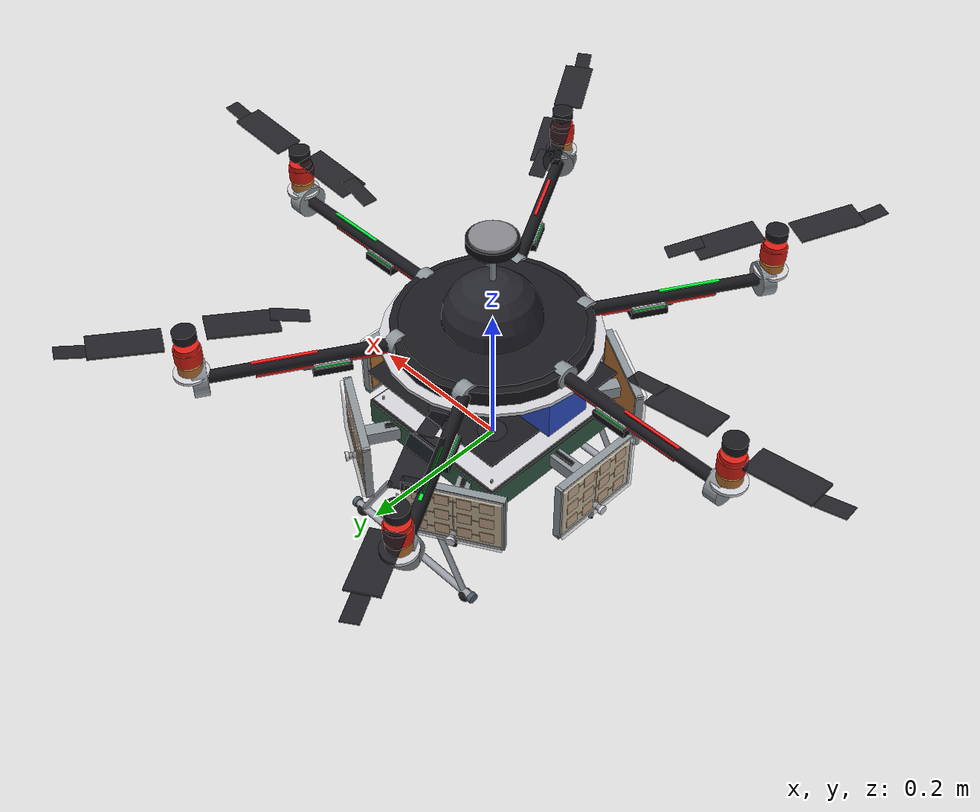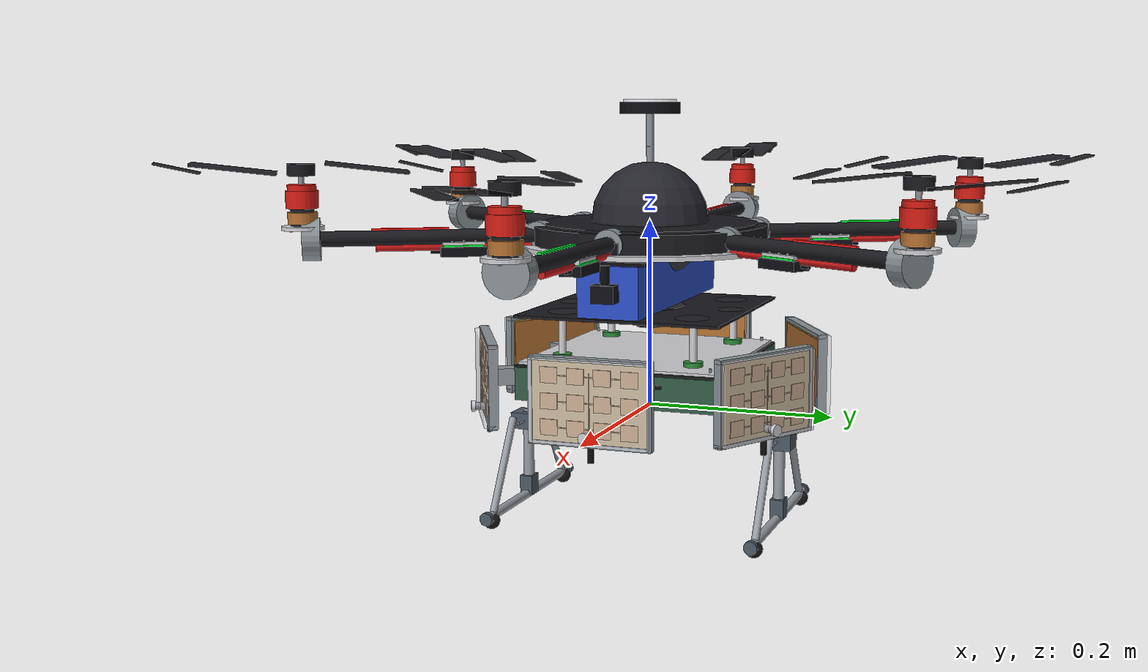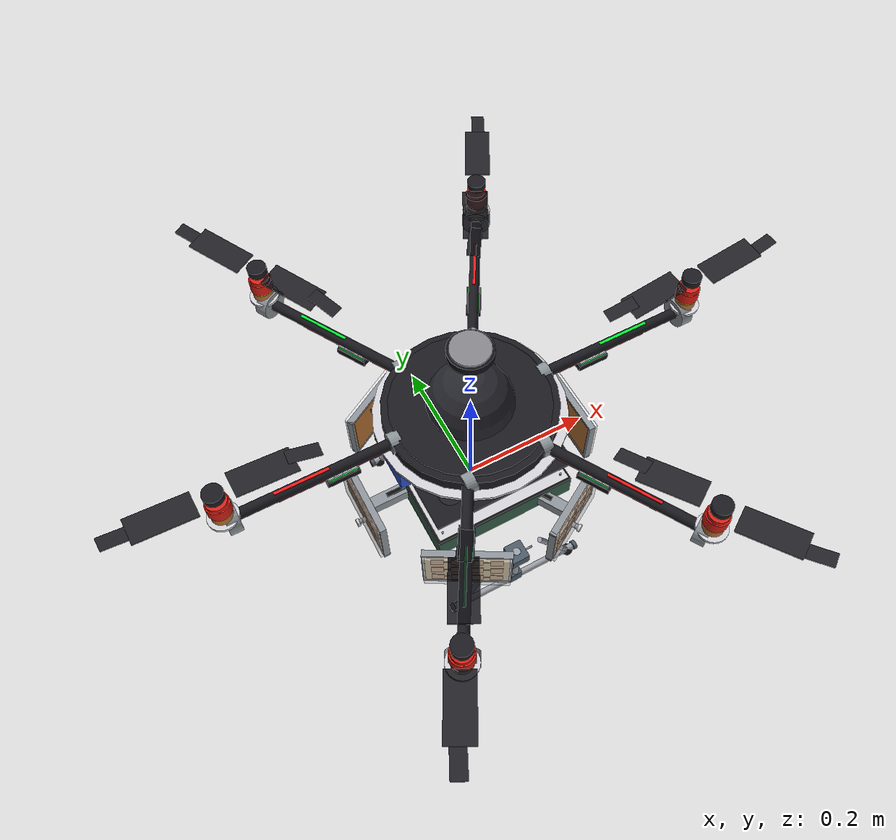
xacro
<?xml version="1.0" encoding="utf-8"?>
<robot name="mbc3_radar_drone" xmlns:xacro="http://ros.org/wiki/xacro">

  <!-- drone_ns: topic prefix for swarm mode.
       Default "" = single-drone (topics: /radar_A/scan etc.)
       Swarm: "drone_L", "drone_S1" etc. (topics: /drone_L/radar_A/scan etc.) -->
  <xacro:arg name="drone_ns" default=""/>
  <xacro:arg name="use_ros2_control" default="true"/>
  <xacro:arg name="viz_scale" default="1.0"/>
  <xacro:property name="ns" value="$(arg drone_ns)"/>
  <xacro:property name="tp" value="${('/' + ns) if ns else ''}"/>

<!-- ═══════════════════════════════════════════════════════════════
     SECTION 1 — CONSTANTS AND PROPERTIES
═══════════════════════════════════════════════════════════════ -->

  <xacro:property name="PI"  value="3.14159265358979323846"/>
  <xacro:property name="D2R" value="${PI/180.0}"/>
  <xacro:property name="viz_scale" value="$(arg viz_scale)"/>

  <!-- ── Aerodynamics ─────────────────────────────────────── -->
  <!-- Rotor thrust coeff Ct and torque coeff Cm (12-inch CF prop) -->
  <xacro:property name="rotor_Ct"   value="1.740e-05"/>  <!-- N·s²/rad²  -->
  <xacro:property name="rotor_Cm"   value="2.450e-07"/>  <!-- N·m·s²/rad²-->
  <xacro:property name="rotor_mass" value="0.022"/>      <!-- kg          -->
  <xacro:property name="rotor_r"    value="0.152"/>      <!-- m, 6-inch radius = 12-inch dia -->

  <!-- ── Frame ──────────────────────────────────────────── -->
  <xacro:property name="hub_r"          value="${0.125*viz_scale}"/>
  <xacro:property name="hub_h"          value="${0.020*viz_scale}"/>
  <xacro:property name="hub_flange_r"   value="${0.138*viz_scale}"/>
  <xacro:property name="hub_flange_h"   value="${0.005*viz_scale}"/>
  <xacro:property name="arm_len"        value="0.360"/>
  <xacro:property name="arm_od"         value="${0.016*viz_scale}"/>
  <xacro:property name="arm_id"         value="${0.012*viz_scale}"/>
  <xacro:property name="arm_clamp_r"    value="${0.022*viz_scale}"/>
  <xacro:property name="arm_clamp_h"    value="${0.018*viz_scale}"/>

  <!-- ── Motor ──────────────────────────────────────────── -->
  <xacro:property name="mbell_r"        value="${0.0165*viz_scale}"/>
  <xacro:property name="mbell_h"        value="${0.018*viz_scale}"/>
  <xacro:property name="mstat_r"        value="${0.012*viz_scale}"/>
  <xacro:property name="mstat_h"        value="${0.022*viz_scale}"/>
  <xacro:property name="mshaft_r"       value="${0.003*viz_scale}"/>
  <xacro:property name="mshaft_h"       value="${0.015*viz_scale}"/>
  <!-- Number of cooling vanes on motor bell -->
  <xacro:property name="bell_vane_w"    value="${0.002*viz_scale}"/>
  <xacro:property name="bell_vane_h"    value="${0.006*viz_scale}"/>

  <!-- ── Propeller ─────────────────────────────────────── -->
  <xacro:property name="prop_r"         value="${0.1524*viz_scale}"/>  <!-- 12-inch -->
  <xacro:property name="phub_r"         value="${0.014*viz_scale}"/>
  <xacro:property name="phub_h"         value="${0.012*viz_scale}"/>
  <xacro:property name="blade_len"      value="${0.130*viz_scale}"/>   <!-- 12-inch blade reach -->
  <xacro:property name="blade_chord"    value="${0.038*viz_scale}"/>
  <xacro:property name="blade_t"        value="${0.003*viz_scale}"/>

  <!-- ── ESC ───────────────────────────────────────────── -->
  <xacro:property name="esc_l"          value="${0.048*viz_scale}"/>
  <xacro:property name="esc_w"          value="${0.022*viz_scale}"/>
  <xacro:property name="esc_h"          value="${0.010*viz_scale}"/>

  <!-- ── Bottom plate ──────────────────────────────────── -->
  <xacro:property name="plate_l"        value="${0.220*viz_scale}"/>
  <xacro:property name="plate_w"        value="${0.220*viz_scale}"/>
  <xacro:property name="plate_t"        value="${0.003*viz_scale}"/>

  <!-- ── Standoff ──────────────────────────────────────── -->
  <xacro:property name="so_r"           value="${0.004*viz_scale}"/>
  <xacro:property name="so_len"         value="${0.045*viz_scale}"/>
  <xacro:property name="so_pcd"         value="${0.072*viz_scale}"/>

  <!-- ── Radar box ─────────────────────────────────────── -->
  <xacro:property name="rbox_l"         value="${0.220*viz_scale}"/>
  <xacro:property name="rbox_w"         value="${0.220*viz_scale}"/>
  <xacro:property name="rbox_h"         value="${0.036*viz_scale}"/>

  <!-- ── Antenna panel ─────────────────────────────────── -->
  <xacro:property name="panel_l"        value="${0.120*viz_scale}"/>
  <xacro:property name="panel_h"        value="${0.080*viz_scale}"/>
  <xacro:property name="panel_t"        value="${0.008*viz_scale}"/>
  <xacro:property name="panel_arm_off"  value="${0.110*viz_scale}"/>
  <xacro:property name="radome_t"       value="${0.005*viz_scale}"/>
  <!-- 24 GHz FMCW: ±30° H-FOV, ±22.5° V-FOV per panel.
       6 panels at 60° spacing × 60° FOV = seamless 360° coverage, zero gaps. -->
  <xacro:property name="radar_h_fov"    value="${60.0*D2R}"/>
  <xacro:property name="radar_v_fov"    value="${45.0*D2R}"/>
  <xacro:property name="radar_range_min" value="0.5"/>
  <xacro:property name="radar_range_max" value="5000.0"/>
  <xacro:property name="radar_res"      value="0.120"/>

  <!-- ── Landing gear ──────────────────────────────────── -->
  <xacro:property name="lg_post_r"      value="${0.006*viz_scale}"/>
  <xacro:property name="lg_post_h"      value="${0.090*viz_scale}"/>
  <xacro:property name="lg_skid_l"      value="${0.220*viz_scale}"/>
  <xacro:property name="lg_skid_r"      value="${0.005*viz_scale}"/>
  <xacro:property name="lg_support_r"   value="${0.004*viz_scale}"/>
  <xacro:property name="lg_y"           value="${0.145*viz_scale}"/>
  <xacro:property name="lg_mount_z"     value="${rbox_z - panel_h/2 - 0.016}"/>
  <xacro:property name="lg_support_top_x"  value="${0.040*viz_scale}"/>
  <xacro:property name="lg_support_foot_x" value="${lg_skid_l/2 - 0.015}"/>
  <xacro:property name="lg_support_top_z"  value="${lg_mount_z}"/>
  <xacro:property name="lg_support_foot_z" value="${lg_mount_z - lg_post_h - 0.005}"/>
  <xacro:property name="lg_support_dx" value="${lg_support_foot_x - lg_support_top_x}"/>
  <xacro:property name="lg_support_dz" value="${lg_support_foot_z - lg_support_top_z}"/>
  <xacro:property name="lg_support_l"  value="${sqrt(lg_support_dx*lg_support_dx + lg_support_dz*lg_support_dz)}"/>
  <xacro:property name="lg_support_pitch" value="${atan2(lg_support_dx, -lg_support_dz)}"/>
  <!-- Gazebo contact surface parameters (skid on concrete) -->
  <xacro:property name="skid_mu1"  value="1.8"/>
  <xacro:property name="skid_mu2"  value="1.8"/>
  <xacro:property name="skid_kp"   value="1e6"/>
  <xacro:property name="skid_kd"   value="100.0"/>

  <!-- ── Battery (6S 10000mAh single pack ~255×65×53mm, 1050g) ── -->
  <xacro:property name="bat_l"          value="${0.255*viz_scale}"/>
  <xacro:property name="bat_w"          value="${0.065*viz_scale}"/>
  <xacro:property name="bat_h"          value="${0.053*viz_scale}"/>

  <!-- ── Mass budget (kg) ──────────────────────────────── -->
  <xacro:property name="m_hub"          value="0.300"/>
  <xacro:property name="m_arm"          value="0.060"/>
  <xacro:property name="m_motor"        value="0.095"/>
  <xacro:property name="m_prop"         value="0.020"/>
  <xacro:property name="m_esc"          value="0.032"/>
  <xacro:property name="m_plate"        value="0.070"/>
  <xacro:property name="m_so"           value="0.010"/>
  <xacro:property name="m_rbox"         value="0.860"/>  <!-- Al shell + AWR1843×6 + Doodle Labs + Jetson Orin NX + misc -->
  <xacro:property name="m_panel"        value="0.055"/>
  <xacro:property name="m_bat"          value="1.050"/>  <!-- 6S 10000mAh single pack -->
  <xacro:property name="m_lg"           value="0.055"/>

  <!-- ── Sensor mass (kg) ──────────────────────────────── -->
  <xacro:property name="m_imu"          value="0.020"/>
  <xacro:property name="m_gps"          value="0.028"/>
  <xacro:property name="m_fcu"          value="0.065"/>
  <xacro:property name="m_flow"         value="0.016"/>
  <xacro:property name="m_baro"         value="0.004"/>
  <xacro:property name="m_mag"          value="0.003"/>

  <!-- ── IMU noise (VectorNav VN-100, datasheet values) ── -->
  <!-- Gyro ARW: 0.0035°/√s → rad/√s -->
  <xacro:property name="imu_gyro_stddev"      value="6.107e-5"/>
  <xacro:property name="imu_gyro_bias_mean"   value="0.0"/>
  <xacro:property name="imu_gyro_bias_stddev" value="8.7266e-5"/>
  <!-- Accel VRW: 0.14 mg/√Hz → m/s²/√s -->
  <xacro:property name="imu_accel_stddev"      value="0.01374"/>
  <xacro:property name="imu_accel_bias_mean"   value="0.0"/>
  <xacro:property name="imu_accel_bias_stddev" value="0.196"/>

  <!-- ── Derived geometry ──────────────────────────────── -->
  <xacro:property name="bat_z"    value="${-hub_h/2 - hub_flange_h - bat_h/2 - 0.006}"/>
  <xacro:property name="plate_z"  value="${bat_z - bat_h/2 - plate_t/2 - 0.004}"/>
  <xacro:property name="rbox_z"   value="${plate_z - plate_t/2 - so_len - rbox_h/2 - 0.004}"/>

<!-- ═══════════════════════════════════════════════════════════════
     SECTION 2 — INERTIA HELPER MACROS
═══════════════════════════════════════════════════════════════ -->

  <!-- Solid cylinder, spin axis Z -->
  <xacro:macro name="icyl" params="m r h">
    <inertia ixx="${m*(3*r*r+h*h)/12}" ixy="0" ixz="0"
             iyy="${m*(3*r*r+h*h)/12}" iyz="0"
             izz="${m*r*r/2}"/>
  </xacro:macro>

  <!-- Hollow thin-walled cylinder, spin axis Z -->
  <xacro:macro name="ihcyl" params="m r_o r_i h">
    <inertia ixx="${m*(3*(r_o*r_o+r_i*r_i)+h*h)/12}" ixy="0" ixz="0"
             iyy="${m*(3*(r_o*r_o+r_i*r_i)+h*h)/12}" iyz="0"
             izz="${m*(r_o*r_o+r_i*r_i)/2}"/>
  </xacro:macro>

  <!-- Solid box -->
  <xacro:macro name="ibox" params="m x y z">
    <inertia ixx="${m*(y*y+z*z)/12}" ixy="0" ixz="0"
             iyy="${m*(x*x+z*z)/12}" iyz="0"
             izz="${m*(x*x+y*y)/12}"/>
  </xacro:macro>

  <!-- Thin rod along X, outer radius r -->
  <xacro:macro name="irod_x" params="m l r">
    <inertia ixx="${m*r*r/2}"           ixy="0" ixz="0"
             iyy="${m*(3*r*r+l*l)/12}"  iyz="0"
             izz="${m*(3*r*r+l*l)/12}"/>
  </xacro:macro>

  <!-- Thin annular disc, axis Z (correct for propeller) -->
  <xacro:macro name="idisc_annular" params="m r_o r_i">
    <inertia ixx="${m*(r_o*r_o+r_i*r_i)/4}" ixy="0" ixz="0"
             iyy="${m*(r_o*r_o+r_i*r_i)/4}" iyz="0"
             izz="${m*(r_o*r_o+r_i*r_i)/2}"/>
  </xacro:macro>

  <!-- Point-mass (for tiny sensor links) -->
  <xacro:macro name="ipoint" params="">
    <inertia ixx="1e-9" ixy="0" ixz="0"
             iyy="1e-9" iyz="0" izz="1e-9"/>
  </xacro:macro>

<!-- ═══════════════════════════════════════════════════════════════
     SECTION 3 — MATERIALS
═══════════════════════════════════════════════════════════════ -->

  <material name="cf_dark">       <color rgba="0.10 0.10 0.12 1.00"/></material>
  <material name="cf_mid">        <color rgba="0.15 0.15 0.18 1.00"/></material>
  <material name="cf_hollow">     <color rgba="0.20 0.20 0.25 0.30"/></material>
  <material name="al_bright">     <color rgba="0.82 0.82 0.84 1.00"/></material>
  <material name="al_dark">       <color rgba="0.55 0.58 0.60 1.00"/></material>
  <material name="al_anodised">   <color rgba="0.30 0.35 0.40 1.00"/></material>
  <material name="motor_bell">    <color rgba="0.85 0.12 0.08 1.00"/></material>
  <material name="motor_stat">    <color rgba="0.12 0.12 0.15 1.00"/></material>
  <material name="copper">        <color rgba="0.72 0.45 0.20 1.00"/></material>
  <material name="prop_cf">       <color rgba="0.08 0.08 0.10 0.88"/></material>
  <material name="esc_body">      <color rgba="0.06 0.06 0.08 1.00"/></material>
  <material name="pcb_grn">       <color rgba="0.72 0.58 0.32 1.00"/></material>
  <material name="radome">        <color rgba="0.94 0.94 0.96 0.55"/></material>
  <material name="radar_hous">    <color rgba="0.20 0.36 0.28 1.00"/></material>
  <material name="steel_bolt">    <color rgba="0.55 0.55 0.58 1.00"/></material>
  <material name="cable">         <color rgba="0.05 0.05 0.06 1.00"/></material>
  <material name="silicone">      <color rgba="0.18 0.55 0.22 1.00"/></material>
  <material name="led_grn">       <color rgba="0.00 1.00 0.20 1.00"/></material>
  <material name="led_red">       <color rgba="1.00 0.10 0.10 1.00"/></material>
  <material name="lipo_blue">     <color rgba="0.18 0.32 0.80 1.00"/></material>
  <material name="lg_al">         <color rgba="0.60 0.62 0.65 1.00"/></material>
  <material name="rubber">        <color rgba="0.10 0.10 0.10 1.00"/></material>
  <material name="foam_white">    <color rgba="0.92 0.92 0.90 1.00"/></material>
  <material name="heat_shrink">   <color rgba="0.80 0.10 0.10 1.00"/></material>
  <material name="solder_mask">   <color rgba="0.04 0.28 0.10 1.00"/></material>

  <xacro:macro name="arm_assembly" params="num angle_deg spin">

    <!-- 4.1  ARM TUBE ─────────────────────────────────────────── -->
    <link name="arm_${num}">
      <inertial>
        <mass value="${m_arm}"/>
        <origin xyz="${arm_len/2} 0 0" rpy="0 0 0"/>
        <!-- Hollow tube inertia: m*(3*(ro²+ri²)+l²)/12 transverse -->
        <inertia ixx="${m_arm*(arm_od/2)*(arm_od/2)/2}"
                 ixy="0" ixz="0"
                 iyy="${m_arm*(3*((arm_od/2)*(arm_od/2)+(arm_id/2)*(arm_id/2))+arm_len*arm_len)/12}"
                 iyz="0"
                 izz="${m_arm*(3*((arm_od/2)*(arm_od/2)+(arm_id/2)*(arm_id/2))+arm_len*arm_len)/12}"/>
      </inertial>
      <!-- outer CF tube -->
      <visual>
        <origin xyz="${arm_len/2} 0 0" rpy="0 ${PI/2} 0"/>
        <geometry><cylinder radius="${arm_od/2}" length="${arm_len}"/></geometry>
        <material name="cf_dark"/>
      </visual>
      <!-- inner hollow (visual only, alpha 0.30) -->
      <visual>
        <origin xyz="${arm_len/2} 0 0" rpy="0 ${PI/2} 0"/>
        <geometry><cylinder radius="${arm_id/2}" length="${arm_len-0.006}"/></geometry>
        <material name="cf_hollow"/>
      </visual>
      <!-- arm-end clamp block -->
      <visual>
        <origin xyz="${arm_len-0.008} 0 0" rpy="0 ${PI/2} 0"/>
        <geometry><cylinder radius="${arm_clamp_r}" length="${arm_clamp_h}"/></geometry>
        <material name="al_dark"/>
      </visual>
      <!-- hub-end clamp block -->
      <visual>
        <origin xyz="0.008 0 0" rpy="0 ${PI/2} 0"/>
        <geometry><cylinder radius="${arm_clamp_r}" length="${arm_clamp_h}"/></geometry>
        <material name="al_dark"/>
      </visual>
      <!-- cable conduit (heat-shrink sleeve on arm underside) -->
      <visual>
        <origin xyz="${arm_len*0.50} 0 ${-arm_od/2-0.002}" rpy="0 ${PI/2} 0"/>
        <geometry><cylinder radius="0.004" length="${arm_len*0.60}"/></geometry>
        <material name="heat_shrink"/>
      </visual>
      <!-- LED status strip (even=green, odd=red) -->
      <xacro:if value="${num % 2 == 0}">
        <visual>
          <origin xyz="${arm_len*0.70} 0 ${arm_od/2+0.001}" rpy="0 0 0"/>
          <geometry><box size="${arm_len*0.22} 0.004 0.002"/></geometry>
          <material name="led_grn"/>
        </visual>
      </xacro:if>
      <xacro:unless value="${num % 2 == 0}">
        <visual>
          <origin xyz="${arm_len*0.70} 0 ${arm_od/2+0.001}" rpy="0 0 0"/>
          <geometry><box size="${arm_len*0.22} 0.004 0.002"/></geometry>
          <material name="led_red"/>
        </visual>
      </xacro:unless>
      <collision>
        <origin xyz="${arm_len/2} 0 0" rpy="0 ${PI/2} 0"/>
        <geometry><cylinder radius="${arm_od/2}" length="${arm_len}"/></geometry>
      </collision>
    </link>

    <joint name="hub_to_arm_${num}" type="fixed">
      <parent link="body_hub"/>
      <child link="arm_${num}"/>
      <origin xyz="0 0 0" rpy="0 0 ${angle_deg * D2R}"/>
    </joint>

    <!-- 4.2  ESC (bolted under arm, 55% along) ──────────────── -->
    <link name="esc_${num}">
      <inertial>
        <mass value="${m_esc}"/>
        <origin xyz="0 0 0" rpy="0 0 0"/>
        <xacro:ibox m="${m_esc}" x="${esc_l}" y="${esc_w}" z="${esc_h}"/>
      </inertial>
      <!-- ESC body -->
      <visual>
        <origin xyz="0 0 0" rpy="0 0 0"/>
        <geometry><box size="${esc_l} ${esc_w} ${esc_h}"/></geometry>
        <material name="esc_body"/>
      </visual>
      <!-- shrink-wrap label -->
      <visual>
        <origin xyz="0 0 ${esc_h/2+0.001}" rpy="0 0 0"/>
        <geometry><box size="${esc_l*0.85} ${esc_w*0.85} 0.002"/></geometry>
        <material name="led_grn"/>
      </visual>
      <!-- Al heatsink fins -->
      <visual>
        <origin xyz="0 0 ${esc_h/2+0.003}" rpy="0 0 0"/>
        <geometry><box size="${esc_l*0.90} ${esc_w*0.75} 0.004"/></geometry>
        <material name="al_bright"/>
      </visual>
      <!-- individual fin strips (3) -->
      <visual><origin xyz="-0.012 0 ${esc_h/2+0.006}" rpy="0 0 0"/>
        <geometry><box size="0.002 ${esc_w*0.65} 0.006"/></geometry><material name="al_bright"/></visual>
      <visual><origin xyz=" 0.000 0 ${esc_h/2+0.006}" rpy="0 0 0"/>
        <geometry><box size="0.002 ${esc_w*0.65} 0.006"/></geometry><material name="al_bright"/></visual>
      <visual><origin xyz=" 0.012 0 ${esc_h/2+0.006}" rpy="0 0 0"/>
        <geometry><box size="0.002 ${esc_w*0.65} 0.006"/></geometry><material name="al_bright"/></visual>
      <!-- power wire stub -->
      <visual>
        <origin xyz="${esc_l/2+0.005} 0 0" rpy="0 ${PI/2} 0"/>
        <geometry><cylinder radius="0.002" length="0.010"/></geometry>
        <material name="cable"/>
      </visual>
      <collision>
        <origin xyz="0 0 0" rpy="0 0 0"/>
        <geometry><box size="${esc_l} ${esc_w} ${esc_h}"/></geometry>
      </collision>
    </link>

    <joint name="arm_to_esc_${num}" type="fixed">
      <parent link="arm_${num}"/>
      <child link="esc_${num}"/>
      <origin xyz="${arm_len*0.55} 0 ${-(arm_od/2+esc_h/2+0.002)}" rpy="0 0 0"/>
    </joint>

    <!-- 4.3  MOTOR STATOR (fixed to arm tip) ────────────────── -->
    <link name="motor_stator_${num}">
      <inertial>
        <mass value="${m_motor*0.45}"/>
        <origin xyz="0 0 ${mstat_h/2}" rpy="0 0 0"/>
        <xacro:icyl m="${m_motor*0.45}" r="${mstat_r}" h="${mstat_h}"/>
      </inertial>
      <!-- stator cylinder -->
      <visual>
        <origin xyz="0 0 ${mstat_h/2}" rpy="0 0 0"/>
        <geometry><cylinder radius="${mstat_r}" length="${mstat_h}"/></geometry>
        <material name="motor_stat"/>
      </visual>
      <!-- copper windings ring -->
      <visual>
        <origin xyz="0 0 ${mstat_h*0.55}" rpy="0 0 0"/>
        <geometry><cylinder radius="${mstat_r+0.003}" length="${mstat_h*0.55}"/></geometry>
        <material name="copper"/>
      </visual>
      <!-- base plate (Al) -->
      <visual>
        <origin xyz="0 0 0.002" rpy="0 0 0"/>
        <geometry><cylinder radius="${mbell_r+0.005}" length="0.004"/></geometry>
        <material name="al_bright"/>
      </visual>
      <!-- 4× M3 mount bolts -->
      <visual><origin xyz=" ${mbell_r*0.72}  0              0.001" rpy="0 0 0"/>
        <geometry><cylinder radius="0.0015" length="0.006"/></geometry><material name="steel_bolt"/></visual>
      <visual><origin xyz="${-mbell_r*0.72}  0              0.001" rpy="0 0 0"/>
        <geometry><cylinder radius="0.0015" length="0.006"/></geometry><material name="steel_bolt"/></visual>
      <visual><origin xyz=" 0               ${mbell_r*0.72} 0.001" rpy="0 0 0"/>
        <geometry><cylinder radius="0.0015" length="0.006"/></geometry><material name="steel_bolt"/></visual>
      <visual><origin xyz=" 0              ${-mbell_r*0.72} 0.001" rpy="0 0 0"/>
        <geometry><cylinder radius="0.0015" length="0.006"/></geometry><material name="steel_bolt"/></visual>
      <collision>
        <origin xyz="0 0 ${mstat_h/2}" rpy="0 0 0"/>
        <geometry><cylinder radius="${mbell_r}" length="${mstat_h}"/></geometry>
      </collision>
    </link>

    <joint name="arm_to_stator_${num}" type="fixed">
      <parent link="arm_${num}"/>
      <child link="motor_stator_${num}"/>
      <origin xyz="${arm_len} 0 ${arm_od/2+0.002}" rpy="0 0 0"/>
    </joint>

    <!-- 4.4  MOTOR BELL (rotating) ─────────────────────────── -->
    <link name="motor_bell_${num}">
      <inertial>
        <mass value="${m_motor*0.55}"/>
        <origin xyz="0 0 ${mbell_h/2}" rpy="0 0 0"/>
        <!-- Hollow bell: treated as thin-walled cylinder -->
        <xacro:ihcyl m="${m_motor*0.55}" r_o="${mbell_r}" r_i="${mbell_r-0.002}" h="${mbell_h}"/>
      </inertial>
      <!-- outer shell -->
      <visual>
        <origin xyz="0 0 ${mbell_h/2}" rpy="0 0 0"/>
        <geometry><cylinder radius="${mbell_r}" length="${mbell_h}"/></geometry>
        <material name="motor_bell"/>
      </visual>
      <!-- top cap -->
      <visual>
        <origin xyz="0 0 ${mbell_h+0.003}" rpy="0 0 0"/>
        <geometry><cylinder radius="${mbell_r-0.002}" length="0.006"/></geometry>
        <material name="motor_bell"/>
      </visual>
      <!-- cooling vanes (4 fins at 90°) -->
      <visual><origin xyz=" ${mbell_r-0.002} 0 ${mbell_h*0.5}" rpy="0 0 0"/>
        <geometry><box size="${bell_vane_w} ${bell_vane_h} ${mbell_h}"/></geometry>
        <material name="motor_bell"/></visual>
      <visual><origin xyz="${-mbell_r+0.002} 0 ${mbell_h*0.5}" rpy="0 0 0"/>
        <geometry><box size="${bell_vane_w} ${bell_vane_h} ${mbell_h}"/></geometry>
        <material name="motor_bell"/></visual>
      <visual><origin xyz="0  ${mbell_r-0.002} ${mbell_h*0.5}" rpy="0 0 0"/>
        <geometry><box size="${bell_vane_h} ${bell_vane_w} ${mbell_h}"/></geometry>
        <material name="motor_bell"/></visual>
      <visual><origin xyz="0 ${-mbell_r+0.002} ${mbell_h*0.5}" rpy="0 0 0"/>
        <geometry><box size="${bell_vane_h} ${bell_vane_w} ${mbell_h}"/></geometry>
        <material name="motor_bell"/></visual>
      <!-- shaft -->
      <visual>
        <origin xyz="0 0 ${mbell_h+0.006+mshaft_h/2}" rpy="0 0 0"/>
        <geometry><cylinder radius="${mshaft_r}" length="${mshaft_h}"/></geometry>
        <material name="steel_bolt"/>
      </visual>
      <!-- prop nut -->
      <visual>
        <origin xyz="0 0 ${mbell_h+0.006+mshaft_h+0.003}" rpy="0 0 0"/>
        <geometry><cylinder radius="0.006" length="0.005"/></geometry>
        <material name="steel_bolt"/>
      </visual>
      <collision>
        <origin xyz="0 0 ${(mbell_h+mshaft_h)/2}" rpy="0 0 0"/>
        <geometry><cylinder radius="${mbell_r}" length="${mbell_h+mshaft_h+0.020}"/></geometry>
      </collision>
    </link>

    <!-- MOTOR SPIN JOINT — continuous, driven by ros2_control -->
    <joint name="motor_${num}_spin" type="continuous">
      <parent link="motor_stator_${num}"/>
      <child link="motor_bell_${num}"/>
      <origin xyz="0 0 ${mstat_h}" rpy="0 0 0"/>
      <axis xyz="0 0 ${spin}"/>
      <dynamics damping="0.0010" friction="0.0002"/>
      <limit effort="18.0" velocity="1500.0"/>
    </joint>

    <!-- 4.5  PROPELLER (hub + 2 blades) ─────────────────────── -->
    <link name="prop_${num}">
      <inertial>
        <mass value="${m_prop}"/>
        <origin xyz="0 0 0" rpy="0 0 0"/>
        <!-- Annular disc: hub bore ≈ 12mm, tip radius prop_r -->
        <xacro:idisc_annular m="${m_prop}" r_o="${prop_r}" r_i="${phub_r}"/>
      </inertial>
      <!-- prop hub collar -->
      <visual>
        <origin xyz="0 0 0" rpy="0 0 0"/>
        <geometry><cylinder radius="${phub_r}" length="${phub_h}"/></geometry>
        <material name="cf_dark"/>
      </visual>
      <!-- blade 1 root section -->
      <visual>
        <origin xyz="${blade_len*0.40+phub_r} 0 0.0015"
                rpy="0 ${-7.0*D2R} ${2.0*D2R}"/>
        <geometry><box size="${blade_len*0.65} ${blade_chord} ${blade_t}"/></geometry>
        <material name="prop_cf"/>
      </visual>
      <!-- blade 1 tip section (tapered) -->
      <visual>
        <origin xyz="${blade_len*0.82+phub_r} 0 0.0025"
                rpy="0 ${-13.0*D2R} ${4.0*D2R}"/>
        <geometry><box size="${blade_len*0.35} ${blade_chord*0.52} ${blade_t*0.65}"/></geometry>
        <material name="prop_cf"/>
      </visual>
      <!-- blade 2 (180° opposite) -->
      <visual>
        <origin xyz="${-(blade_len*0.40+phub_r)} 0 0.0015"
                rpy="0 ${-7.0*D2R} ${2.0*D2R}"/>
        <geometry><box size="${blade_len*0.65} ${blade_chord} ${blade_t}"/></geometry>
        <material name="prop_cf"/>
      </visual>
      <visual>
        <origin xyz="${-(blade_len*0.82+phub_r)} 0 0.0025"
                rpy="0 ${-13.0*D2R} ${-4.0*D2R}"/>
        <geometry><box size="${blade_len*0.35} ${blade_chord*0.52} ${blade_t*0.65}"/></geometry>
        <material name="prop_cf"/>
      </visual>
      <collision>
        <origin xyz="0 0 0.002" rpy="0 0 0"/>
        <geometry><cylinder radius="${prop_r}" length="0.005"/></geometry>
      </collision>
    </link>

    <joint name="bell_to_prop_${num}" type="fixed">
      <parent link="motor_bell_${num}"/>
      <child link="prop_${num}"/>
      <origin xyz="0 0 ${mbell_h+0.006+mshaft_h}" rpy="0 0 0"/>
    </joint>

  </xacro:macro>

  <xacro:macro name="antenna_panel" params="id angle_deg">

    <!-- 5.1  PANEL ARM CONNECTOR ─────────────────────────────── -->
    <link name="panel_arm_${id}">
      <inertial>
        <mass value="0.014"/>
        <origin xyz="0.030 0 0" rpy="0 0 0"/>
        <xacro:ibox m="0.014" x="0.060" y="0.018" z="0.018"/>
      </inertial>
      <visual>
        <origin xyz="0.030 0 0" rpy="0 0 0"/>
        <geometry><box size="0.060 0.018 0.018"/></geometry>
        <material name="al_dark"/>
      </visual>
      <!-- cable guide channel -->
      <visual>
        <origin xyz="0.015 0 0.010" rpy="0 0 0"/>
        <geometry><box size="0.030 0.006 0.004"/></geometry>
        <material name="cable"/>
      </visual>
      <!-- mounting bolt fore -->
      <visual>
        <origin xyz="0.050 0 0" rpy="0 ${PI/2} 0"/>
        <geometry><cylinder radius="0.0015" length="0.008"/></geometry>
        <material name="steel_bolt"/>
      </visual>
      <!-- mounting bolt aft -->
      <visual>
        <origin xyz="0.010 0 0" rpy="0 ${PI/2} 0"/>
        <geometry><cylinder radius="0.0015" length="0.008"/></geometry>
        <material name="steel_bolt"/>
      </visual>
      <collision>
        <origin xyz="0.030 0 0" rpy="0 0 0"/>
        <geometry><box size="0.060 0.018 0.018"/></geometry>
      </collision>
    </link>

    <!-- Panel arm origin at each face of radar_box.
         The xyz offset vector is rotated by angle_deg so each panel
         originates at its own face (not always the +X face). -->
    <joint name="rbox_to_arm_${id}" type="fixed">
      <parent link="radar_box"/>
      <child link="panel_arm_${id}"/>
      <origin xyz="${panel_arm_off * cos(angle_deg * D2R)} ${panel_arm_off * sin(angle_deg * D2R)} 0"
              rpy="0 0 ${angle_deg * D2R}"/>
    </joint>

    <!-- 5.2  ANTENNA PANEL PCB (Rogers 4003C substrate) ──────── -->
    <link name="antenna_panel_${id}">
      <inertial>
        <mass value="${m_panel}"/>
        <origin xyz="0 0 0" rpy="0 0 0"/>
        <xacro:ibox m="${m_panel}" x="${panel_t}" y="${panel_l}" z="${panel_h}"/>
      </inertial>

      <!-- PCB substrate -->
      <visual>
        <origin xyz="0 0 0" rpy="0 0 0"/>
        <geometry><box size="${panel_t} ${panel_l} ${panel_h}"/></geometry>
        <material name="pcb_grn"/>
      </visual>
      <!-- ground plane copper layer (back face) -->
      <visual>
        <origin xyz="${-panel_t/2-0.0002} 0 0" rpy="0 0 0"/>
        <geometry><box size="0.0004 ${panel_l-0.004} ${panel_h-0.004}"/></geometry>
        <material name="copper"/>
      </visual>

      <!-- 4×3 patch array — 24 GHz radiating elements -->
      <!-- Row z=-0.026 -->
      <visual><origin xyz="${panel_t/2+0.001} -0.042 -0.026" rpy="0 0 0"/>
        <geometry><box size="0.001 0.018 0.016"/></geometry><material name="copper"/></visual>
      <visual><origin xyz="${panel_t/2+0.001} -0.014 -0.026" rpy="0 0 0"/>
        <geometry><box size="0.001 0.018 0.016"/></geometry><material name="copper"/></visual>
      <visual><origin xyz="${panel_t/2+0.001}  0.014 -0.026" rpy="0 0 0"/>
        <geometry><box size="0.001 0.018 0.016"/></geometry><material name="copper"/></visual>
      <visual><origin xyz="${panel_t/2+0.001}  0.042 -0.026" rpy="0 0 0"/>
        <geometry><box size="0.001 0.018 0.016"/></geometry><material name="copper"/></visual>
      <!-- Row z=0 -->
      <visual><origin xyz="${panel_t/2+0.001} -0.042  0.000" rpy="0 0 0"/>
        <geometry><box size="0.001 0.018 0.016"/></geometry><material name="copper"/></visual>
      <visual><origin xyz="${panel_t/2+0.001} -0.014  0.000" rpy="0 0 0"/>
        <geometry><box size="0.001 0.018 0.016"/></geometry><material name="copper"/></visual>
      <visual><origin xyz="${panel_t/2+0.001}  0.014  0.000" rpy="0 0 0"/>
        <geometry><box size="0.001 0.018 0.016"/></geometry><material name="copper"/></visual>
      <visual><origin xyz="${panel_t/2+0.001}  0.042  0.000" rpy="0 0 0"/>
        <geometry><box size="0.001 0.018 0.016"/></geometry><material name="copper"/></visual>
      <!-- Row z=+0.026 -->
      <visual><origin xyz="${panel_t/2+0.001} -0.042  0.026" rpy="0 0 0"/>
        <geometry><box size="0.001 0.018 0.016"/></geometry><material name="copper"/></visual>
      <visual><origin xyz="${panel_t/2+0.001} -0.014  0.026" rpy="0 0 0"/>
        <geometry><box size="0.001 0.018 0.016"/></geometry><material name="copper"/></visual>
      <visual><origin xyz="${panel_t/2+0.001}  0.014  0.026" rpy="0 0 0"/>
        <geometry><box size="0.001 0.018 0.016"/></geometry><material name="copper"/></visual>
      <visual><origin xyz="${panel_t/2+0.001}  0.042  0.026" rpy="0 0 0"/>
        <geometry><box size="0.001 0.018 0.016"/></geometry><material name="copper"/></visual>

      <!-- Feed network traces (horizontal runners) -->
      <visual><origin xyz="${panel_t/2+0.0005}  0.000 -0.026" rpy="0 0 0"/>
        <geometry><box size="0.0005 0.092 0.001"/></geometry><material name="copper"/></visual>
      <visual><origin xyz="${panel_t/2+0.0005}  0.000  0.000" rpy="0 0 0"/>
        <geometry><box size="0.0005 0.092 0.001"/></geometry><material name="copper"/></visual>
      <visual><origin xyz="${panel_t/2+0.0005}  0.000  0.026" rpy="0 0 0"/>
        <geometry><box size="0.0005 0.092 0.001"/></geometry><material name="copper"/></visual>
      <!-- Vertical feed trunk -->
      <visual><origin xyz="${panel_t/2+0.0005}  0.000  0.000" rpy="0 0 0"/>
        <geometry><box size="0.0005 0.001 0.060"/></geometry><material name="copper"/></visual>

      <!-- PTFE radome cover (RF-transparent) -->
      <visual>
        <origin xyz="${panel_t/2+radome_t/2+0.001} 0 0" rpy="0 0 0"/>
        <geometry><box size="${radome_t} ${panel_l+0.004} ${panel_h+0.004}"/></geometry>
        <material name="radome"/>
      </visual>

      <!-- Al border frame — top/bottom/left/right -->
      <visual><origin xyz="0 0  ${panel_h/2+0.002}" rpy="0 0 0"/>
        <geometry><box size="${panel_t+0.002} ${panel_l+0.008} 0.004"/></geometry>
        <material name="al_dark"/></visual>
      <visual><origin xyz="0 0 ${-panel_h/2-0.002}" rpy="0 0 0"/>
        <geometry><box size="${panel_t+0.002} ${panel_l+0.008} 0.004"/></geometry>
        <material name="al_dark"/></visual>
      <visual><origin xyz="0  ${panel_l/2+0.002} 0" rpy="0 0 0"/>
        <geometry><box size="${panel_t+0.002} 0.004 ${panel_h+0.008}"/></geometry>
        <material name="al_dark"/></visual>
      <visual><origin xyz="0 ${-panel_l/2-0.002} 0" rpy="0 0 0"/>
        <geometry><box size="${panel_t+0.002} 0.004 ${panel_h+0.008}"/></geometry>
        <material name="al_dark"/></visual>

      <!-- SMA RF connector + hex nut -->
      <visual>
        <origin xyz="${panel_t/2+0.006} 0 ${-panel_h/2+0.008}" rpy="0 ${PI/2} 0"/>
        <geometry><cylinder radius="0.004" length="0.012"/></geometry>
        <material name="steel_bolt"/>
      </visual>
      <visual>
        <origin xyz="${panel_t/2+0.013} 0 ${-panel_h/2+0.008}" rpy="0 ${PI/2} 0"/>
        <geometry><cylinder radius="0.006" length="0.004"/></geometry>
        <material name="al_bright"/>
      </visual>
      <!-- RF coax to radar_box -->
      <visual>
        <origin xyz="0 0 ${-panel_h/2-0.010}" rpy="0 0 0"/>
        <geometry><cylinder radius="0.003" length="0.020"/></geometry>
        <material name="cable"/>
      </visual>

      <collision>
        <origin xyz="${(panel_t+radome_t)/2} 0 0" rpy="0 0 0"/>
        <geometry>
          <box size="${panel_t+radome_t+0.002} ${panel_l+0.012} ${panel_h+0.012}"/>
        </geometry>
      </collision>
    </link>

    <joint name="arm_to_panel_${id}" type="fixed">
      <parent link="panel_arm_${id}"/>
      <child link="antenna_panel_${id}"/>
      <origin xyz="0.064 0 0" rpy="0 0 0"/>
    </joint>

    <!-- 5.3  RADAR SENSOR FRAME (virtual, no geometry) ───────── -->
    <link name="radar_frame_${id}">
      <inertial>
        <mass value="0.001"/>
        <origin xyz="0 0 0" rpy="0 0 0"/>
        <xacro:ipoint/>
      </inertial>
    </link>
    <joint name="panel_to_rframe_${id}" type="fixed">
      <parent link="antenna_panel_${id}"/>
      <child link="radar_frame_${id}"/>
      <!-- at radiating face (front of radome) -->
      <origin xyz="${panel_t/2+radome_t+0.003} 0 0" rpy="0 0 0"/>
    </joint>

  </xacro:macro>

<!-- ═══════════════════════════════════════════════════════════════
     SECTION 6 — LANDING GEAR MACRO
═══════════════════════════════════════════════════════════════ -->

  <xacro:macro name="landing_gear" params="side y_sign">

    <!-- Vertical post -->
    <link name="lg_post_${side}">
      <inertial>
        <mass value="${m_lg*0.55}"/>
        <origin xyz="0 0 ${-lg_post_h/2}" rpy="0 0 0"/>
        <xacro:icyl m="${m_lg*0.55}" r="${lg_post_r}" h="${lg_post_h}"/>
      </inertial>
      <visual>
        <origin xyz="0 0 ${-lg_post_h/2}" rpy="0 0 0"/>
        <geometry><cylinder radius="${lg_post_r}" length="${lg_post_h}"/></geometry>
        <material name="lg_al"/>
      </visual>
      <!-- saddle clamp block at top -->
      <visual>
        <origin xyz="0 0 -0.010" rpy="0 0 0"/>
        <geometry><box size="0.028 0.030 0.018"/></geometry>
        <material name="al_anodised"/>
      </visual>
      <!-- clamp bolt pair -->
      <visual>
        <origin xyz="0.012 0 -0.010" rpy="0 ${PI/2} 0"/>
        <geometry><cylinder radius="0.0015" length="0.030"/></geometry>
        <material name="steel_bolt"/>
      </visual>
      <visual>
        <origin xyz="-0.012 0 -0.010" rpy="0 ${PI/2} 0"/>
        <geometry><cylinder radius="0.0015" length="0.030"/></geometry>
        <material name="steel_bolt"/>
      </visual>
      <collision>
        <origin xyz="0 0 ${-lg_post_h/2}" rpy="0 0 0"/>
        <geometry><cylinder radius="${lg_post_r+0.002}" length="${lg_post_h}"/></geometry>
      </collision>
    </link>

    <joint name="hub_to_lg_${side}" type="fixed">
      <parent link="body_hub"/>
      <child link="lg_post_${side}"/>
      <origin xyz="0 ${y_sign*lg_y} ${lg_mount_z}" rpy="0 0 0"/>
    </joint>

    <!-- Horizontal skid rail -->
    <link name="lg_skid_${side}">
      <inertial>
        <mass value="${m_lg*0.45}"/>
        <origin xyz="0 0 0" rpy="0 0 0"/>
        <xacro:irod_x m="${m_lg*0.45}" l="${lg_skid_l}" r="${lg_skid_r}"/>
      </inertial>
      <!-- skid tube -->
      <visual>
        <origin xyz="0 0 0" rpy="0 ${PI/2} 0"/>
        <geometry><cylinder radius="${lg_skid_r}" length="${lg_skid_l}"/></geometry>
        <material name="lg_al"/>
      </visual>
      <!-- cross brace connector (slim vertical plate) -->
      <visual>
        <origin xyz="0 0 0.010" rpy="0 0 0"/>
        <geometry><box size="0.018 ${lg_skid_r*2+0.004} 0.022"/></geometry>
        <material name="al_anodised"/>
      </visual>
      <!-- rubber feet (front and rear) -->
      <visual>
        <origin xyz="${lg_skid_l/2-0.012} 0 -0.005" rpy="0 0 0"/>
        <geometry><sphere radius="0.009"/></geometry>
        <material name="rubber"/>
      </visual>
      <visual>
        <origin xyz="${-(lg_skid_l/2-0.012)} 0 -0.005" rpy="0 0 0"/>
        <geometry><sphere radius="0.009"/></geometry>
        <material name="rubber"/>
      </visual>
      <!-- end caps -->
      <visual>
        <origin xyz="${ lg_skid_l/2} 0 0" rpy="0 ${PI/2} 0"/>
        <geometry><cylinder radius="${lg_skid_r+0.002}" length="0.006"/></geometry>
        <material name="al_anodised"/>
      </visual>
      <visual>
        <origin xyz="${-lg_skid_l/2} 0 0" rpy="0 ${PI/2} 0"/>
        <geometry><cylinder radius="${lg_skid_r+0.002}" length="0.006"/></geometry>
        <material name="al_anodised"/>
      </visual>
      <!-- collision: slightly enlarged for stable contact -->
      <collision>
        <origin xyz="0 0 -0.005" rpy="0 ${PI/2} 0"/>
        <geometry><cylinder radius="${lg_skid_r+0.009}" length="${lg_skid_l}"/></geometry>
      </collision>
    </link>

    <joint name="lg_post_to_skid_${side}" type="fixed">
      <parent link="lg_post_${side}"/>
      <child link="lg_skid_${side}"/>
      <origin xyz="0 0 ${-lg_post_h-0.005}" rpy="0 0 0"/>
    </joint>

    <!-- Front diagonal support tube -->
    <link name="lg_support_front_${side}">
      <inertial>
        <mass value="${m_lg*0.18}"/>
        <origin xyz="0 0 0" rpy="0 0 0"/>
        <xacro:icyl m="${m_lg*0.18}" r="${lg_support_r}" h="${lg_support_l}"/>
      </inertial>
      <visual>
        <origin xyz="0 0 0" rpy="0 ${-lg_support_pitch} 0"/>
        <geometry><cylinder radius="${lg_support_r}" length="${lg_support_l}"/></geometry>
        <material name="lg_al"/>
      </visual>
      <collision>
        <origin xyz="0 0 0" rpy="0 ${-lg_support_pitch} 0"/>
        <geometry><cylinder radius="${lg_support_r+0.001}" length="${lg_support_l}"/></geometry>
      </collision>
    </link>

    <joint name="hub_to_lg_support_front_${side}" type="fixed">
      <parent link="body_hub"/>
      <child link="lg_support_front_${side}"/>
      <origin xyz="${(lg_support_top_x + lg_support_foot_x)/2} ${y_sign*lg_y} ${(lg_support_top_z + lg_support_foot_z)/2}" rpy="0 0 0"/>
    </joint>

    <!-- Rear diagonal support tube -->
    <link name="lg_support_rear_${side}">
      <inertial>
        <mass value="${m_lg*0.18}"/>
        <origin xyz="0 0 0" rpy="0 0 0"/>
        <xacro:icyl m="${m_lg*0.18}" r="${lg_support_r}" h="${lg_support_l}"/>
      </inertial>
      <visual>
        <origin xyz="0 0 0" rpy="0 ${lg_support_pitch} 0"/>
        <geometry><cylinder radius="${lg_support_r}" length="${lg_support_l}"/></geometry>
        <material name="lg_al"/>
      </visual>
      <collision>
        <origin xyz="0 0 0" rpy="0 ${lg_support_pitch} 0"/>
        <geometry><cylinder radius="${lg_support_r+0.001}" length="${lg_support_l}"/></geometry>
      </collision>
    </link>

    <joint name="hub_to_lg_support_rear_${side}" type="fixed">
      <parent link="body_hub"/>
      <child link="lg_support_rear_${side}"/>
      <origin xyz="${-(lg_support_top_x + lg_support_foot_x)/2} ${y_sign*lg_y} ${(lg_support_top_z + lg_support_foot_z)/2}" rpy="0 0 0"/>
    </joint>

  </xacro:macro>

<!-- ═══════════════════════════════════════════════════════════════
     SECTION 7 — STANDOFF + VIBRATION-DAMPER MACRO
═══════════════════════════════════════════════════════════════ -->

  <xacro:macro name="standoff" params="id px py">
    <link name="standoff_${id}">
      <inertial>
        <mass value="${m_so}"/>
        <origin xyz="0 0 ${-so_len/2}" rpy="0 0 0"/>
        <xacro:icyl m="${m_so}" r="${so_r}" h="${so_len}"/>
      </inertial>
      <!-- hex standoff body -->
      <visual>
        <origin xyz="0 0 ${-so_len/2}" rpy="0 0 ${PI/6}"/>
        <geometry><cylinder radius="${so_r}" length="${so_len}"/></geometry>
        <material name="al_bright"/>
      </visual>
      <!-- upper M4 thread stub -->
      <visual>
        <origin xyz="0 0 -0.004" rpy="0 0 0"/>
        <geometry><cylinder radius="${so_r*0.65}" length="0.008"/></geometry>
        <material name="steel_bolt"/>
      </visual>
      <!-- lower M4 thread stub -->
      <visual>
        <origin xyz="0 0 ${-so_len+0.004}" rpy="0 0 0"/>
        <geometry><cylinder radius="${so_r*0.65}" length="0.008"/></geometry>
        <material name="steel_bolt"/>
      </visual>
      <!-- silicone vibration-isolation damper disc (top) -->
      <visual>
        <origin xyz="0 0 -0.001" rpy="0 0 0"/>
        <geometry><cylinder radius="0.010" length="0.006"/></geometry>
        <material name="silicone"/>
      </visual>
      <!-- silicone damper disc (bottom) -->
      <visual>
        <origin xyz="0 0 ${-so_len+0.001}" rpy="0 0 0"/>
        <geometry><cylinder radius="0.010" length="0.006"/></geometry>
        <material name="silicone"/>
      </visual>
      <collision>
        <origin xyz="0 0 ${-so_len/2}" rpy="0 0 0"/>
        <geometry><cylinder radius="${so_r}" length="${so_len}"/></geometry>
      </collision>
    </link>
    <joint name="plate_to_so_${id}" type="fixed">
      <parent link="bottom_plate"/>
      <child link="standoff_${id}"/>
      <origin xyz="${px} ${py} ${-plate_t/2}" rpy="0 0 0"/>
    </joint>
  </xacro:macro>

<!-- ═══════════════════════════════════════════════════════════════
     SECTION 8 — BASE LINK
═══════════════════════════════════════════════════════════════ -->

  <link name="base_link"/>

<!-- ═══════════════════════════════════════════════════════════════
     SECTION 9 — BODY HUB (multi-body realistic)
═══════════════════════════════════════════════════════════════ -->

  <link name="body_hub">
    <inertial>
      <mass value="${m_hub}"/>
      <origin xyz="0 0 0" rpy="0 0 0"/>
      <xacro:icyl m="${m_hub}" r="${hub_r}" h="${hub_h}"/>
    </inertial>

    <!-- main CF cylinder body -->
    <visual>
      <origin xyz="0 0 0" rpy="0 0 0"/>
      <geometry><cylinder radius="${hub_r}" length="${hub_h}"/></geometry>
      <material name="cf_dark"/>
    </visual>
    <!-- top CF dome cap -->
    <visual>
      <origin xyz="0 0 ${hub_h/2+0.004}" rpy="0 0 0"/>
      <geometry><sphere radius="${hub_r*0.50}"/></geometry>
      <material name="cf_mid"/>
    </visual>
    <!-- top plate ring -->
    <visual>
      <origin xyz="0 0 ${hub_h/2+0.001}" rpy="0 0 0"/>
      <geometry><cylinder radius="${hub_r*0.92}" length="0.003"/></geometry>
      <material name="cf_dark"/>
    </visual>
    <!-- centre status LED ring -->
    <visual>
      <origin xyz="0 0 ${hub_h/2+0.002}" rpy="0 0 0"/>
      <geometry><cylinder radius="${hub_r*0.28}" length="0.003"/></geometry>
      <material name="led_grn"/>
    </visual>
    <!-- PDB (power distribution board) ring -->
    <visual>
      <origin xyz="0 0 ${-hub_h/4}" rpy="0 0 0"/>
      <geometry><cylinder radius="${hub_r*0.72}" length="0.004"/></geometry>
      <material name="pcb_grn"/>
    </visual>
    <!-- main XT90-S power connector (front face) -->
    <visual>
      <origin xyz="${hub_r-0.005} 0 ${-hub_h/4}" rpy="0 ${PI/2} 0"/>
      <geometry><box size="0.014 0.022 0.016"/></geometry>
      <material name="esc_body"/>
    </visual>
    <!-- bottom Al flange ring -->
    <visual>
      <origin xyz="0 0 ${-hub_h/2-hub_flange_h/2}" rpy="0 0 0"/>
      <geometry><cylinder radius="${hub_flange_r}" length="${hub_flange_h}"/></geometry>
      <material name="al_bright"/>
    </visual>
    <!-- 6 arm root boss rings (one per arm, at 60° increments) -->
    <visual><origin xyz="${hub_r*0.94} 0 0" rpy="0 ${PI/2} 0"/>
      <geometry><cylinder radius="0.015" length="0.016"/></geometry><material name="al_dark"/></visual>
    <visual><origin xyz="${hub_r*0.94*0.5} ${hub_r*0.94*0.866} 0" rpy="0 ${PI/2} 0"/>
      <geometry><cylinder radius="0.015" length="0.016"/></geometry><material name="al_dark"/></visual>
    <visual><origin xyz="${-hub_r*0.94*0.5} ${hub_r*0.94*0.866} 0" rpy="0 ${PI/2} 0"/>
      <geometry><cylinder radius="0.015" length="0.016"/></geometry><material name="al_dark"/></visual>
    <visual><origin xyz="${-hub_r*0.94} 0 0" rpy="0 ${PI/2} 0"/>
      <geometry><cylinder radius="0.015" length="0.016"/></geometry><material name="al_dark"/></visual>
    <visual><origin xyz="${-hub_r*0.94*0.5} ${-hub_r*0.94*0.866} 0" rpy="0 ${PI/2} 0"/>
      <geometry><cylinder radius="0.015" length="0.016"/></geometry><material name="al_dark"/></visual>
    <visual><origin xyz="${hub_r*0.94*0.5} ${-hub_r*0.94*0.866} 0" rpy="0 ${PI/2} 0"/>
      <geometry><cylinder radius="0.015" length="0.016"/></geometry><material name="al_dark"/></visual>

    <collision>
      <origin xyz="0 0 0" rpy="0 0 0"/>
      <geometry><cylinder radius="${hub_flange_r}" length="${hub_h+0.030}"/></geometry>
    </collision>
  </link>

  <joint name="base_to_body" type="fixed">
    <parent link="base_link"/>
    <child link="body_hub"/>
    <!-- Total ground-to-GPS height ≈ 280 mm per design spec -->
    <origin xyz="0 0 0.1865" rpy="0 0 0"/>
  </joint>

<!-- ═══════════════════════════════════════════════════════════════
     SECTION 10 — BATTERY (LiPo 6S 16000 mAh × 2)
═══════════════════════════════════════════════════════════════ -->

  <link name="battery">
    <inertial>
      <mass value="${m_bat}"/>
      <origin xyz="0 0 0" rpy="0 0 0"/>
      <xacro:ibox m="${m_bat}" x="${bat_l}" y="${bat_w}" z="${bat_h}"/>
    </inertial>
    <!-- single 6S 10000mAh pack -->
    <visual>
      <origin xyz="0 0 0" rpy="0 0 0"/>
      <geometry><box size="${bat_l} ${bat_w} ${bat_h}"/></geometry>
      <material name="lipo_blue"/>
    </visual>
    <!-- label wrap -->
    <visual>
      <origin xyz="0 0 ${bat_h/2+0.001}" rpy="0 0 0"/>
      <geometry><box size="${bat_l*0.85} ${bat_w*0.85} 0.002"/></geometry>
      <material name="cable"/>
    </visual>
    <!-- velcro straps (front/rear) -->
    <visual>
      <origin xyz="${bat_l/2-0.015} 0 ${bat_h/2+0.002}" rpy="0 0 0"/>
      <geometry><box size="0.022 ${bat_w+0.010} 0.004"/></geometry>
      <material name="cable"/>
    </visual>
    <visual>
      <origin xyz="${-(bat_l/2-0.015)} 0 ${bat_h/2+0.002}" rpy="0 0 0"/>
      <geometry><box size="0.022 ${bat_w+0.010} 0.004"/></geometry>
      <material name="cable"/>
    </visual>
    <!-- XT90-S connector -->
    <visual>
      <origin xyz="${bat_l/2+0.007} 0 0" rpy="0 ${PI/2} 0"/>
      <geometry><box size="0.018 0.024 0.018"/></geometry>
      <material name="esc_body"/>
    </visual>
    <!-- balance lead (13S wire bundle) -->
    <visual>
      <origin xyz="${bat_l/2+0.007} 0 ${bat_h/4}" rpy="0 0 0"/>
      <geometry><cylinder radius="0.005" length="0.030"/></geometry>
      <material name="cable"/>
    </visual>
    <!-- foam pad top -->
    <visual>
      <origin xyz="0 0 ${bat_h/2+0.003}" rpy="0 0 0"/>
      <geometry><box size="${bat_l*0.90} ${bat_w*0.90} 0.004"/></geometry>
      <material name="foam_white"/>
    </visual>
    <collision>
      <origin xyz="0 0 0" rpy="0 0 0"/>
      <geometry><box size="${bat_l+0.010} ${bat_w+0.010} ${bat_h+0.006}"/></geometry>
    </collision>
  </link>

  <joint name="hub_to_battery" type="fixed">
    <parent link="body_hub"/>
    <child link="battery"/>
    <!-- bat_z computed with explicit clearance from hub_flange bottom.
         v1 had 1mm clearance between battery top and ESC bottoms.
         bat_z = -(hub_h/2 + hub_flange_h + bat_h/2 + 0.006) -->
    <origin xyz="0 0 ${bat_z}" rpy="0 0 0"/>
  </joint>

<!-- ═══════════════════════════════════════════════════════════════
     SECTION 11 — BOTTOM PLATE (CNC-cut CF)
═══════════════════════════════════════════════════════════════ -->

  <link name="bottom_plate">
    <inertial>
      <mass value="${m_plate}"/>
      <origin xyz="0 0 0" rpy="0 0 0"/>
      <xacro:ibox m="${m_plate}" x="${plate_l}" y="${plate_w}" z="${plate_t}"/>
    </inertial>
    <!-- main plate -->
    <visual>
      <origin xyz="0 0 0" rpy="0 0 0"/>
      <geometry><box size="${plate_l} ${plate_w} ${plate_t}"/></geometry>
      <material name="cf_dark"/>
    </visual>
    <!-- engraved centre circle -->
    <visual>
      <origin xyz="0 0 ${plate_t/2+0.0002}" rpy="0 0 0"/>
      <geometry><cylinder radius="0.038" length="0.001"/></geometry>
      <material name="cf_mid"/>
    </visual>
    <!-- weight-saving hex pockets -->
    <visual><origin xyz=" 0.070  0.070 ${plate_t/2+0.0002}" rpy="0 0 0"/>
      <geometry><cylinder radius="0.018" length="0.001"/></geometry><material name="cf_hollow"/></visual>
    <visual><origin xyz="-0.070  0.070 ${plate_t/2+0.0002}" rpy="0 0 0"/>
      <geometry><cylinder radius="0.018" length="0.001"/></geometry><material name="cf_hollow"/></visual>
    <visual><origin xyz=" 0.070 -0.070 ${plate_t/2+0.0002}" rpy="0 0 0"/>
      <geometry><cylinder radius="0.018" length="0.001"/></geometry><material name="cf_hollow"/></visual>
    <visual><origin xyz="-0.070 -0.070 ${plate_t/2+0.0002}" rpy="0 0 0"/>
      <geometry><cylinder radius="0.018" length="0.001"/></geometry><material name="cf_hollow"/></visual>
    <visual><origin xyz=" 0.000  0.090 ${plate_t/2+0.0002}" rpy="0 0 0"/>
      <geometry><cylinder radius="0.014" length="0.001"/></geometry><material name="cf_hollow"/></visual>
    <visual><origin xyz=" 0.000 -0.090 ${plate_t/2+0.0002}" rpy="0 0 0"/>
      <geometry><cylinder radius="0.014" length="0.001"/></geometry><material name="cf_hollow"/></visual>
    <collision>
      <origin xyz="0 0 0" rpy="0 0 0"/>
      <geometry><box size="${plate_l} ${plate_w} ${plate_t}"/></geometry>
    </collision>
  </link>

  <joint name="hub_to_plate" type="fixed">
    <parent link="body_hub"/>
    <child link="bottom_plate"/>
    <origin xyz="0 0 ${plate_z}" rpy="0 0 0"/>
  </joint>

<!-- ═══════════════════════════════════════════════════════════════
     SECTION 12 — RADAR ELECTRONICS BOX
═══════════════════════════════════════════════════════════════ -->

  <link name="radar_box">
    <inertial>
      <mass value="${m_rbox}"/>
      <origin xyz="0 0 0" rpy="0 0 0"/>
      <xacro:ibox m="${m_rbox}" x="${rbox_l}" y="${rbox_w}" z="${rbox_h}"/>
    </inertial>

    <!-- outer Al 5052 shell -->
    <visual>
      <origin xyz="0 0 0" rpy="0 0 0"/>
      <geometry><box size="${rbox_l} ${rbox_w} ${rbox_h}"/></geometry>
      <material name="radar_hous"/>
    </visual>
    <!-- removable Al lid (top face) -->
    <visual>
      <origin xyz="0 0 ${rbox_h/2+0.002}" rpy="0 0 0"/>
      <geometry><box size="${rbox_l-0.006} ${rbox_w-0.006} 0.004"/></geometry>
      <material name="al_bright"/>
    </visual>
    <!-- lid M3 screws — 4 corners -->
    <visual><origin xyz=" ${rbox_l/2-0.012}  ${rbox_w/2-0.012} ${rbox_h/2+0.005}" rpy="0 0 0"/>
      <geometry><cylinder radius="0.0015" length="0.006"/></geometry><material name="steel_bolt"/></visual>
    <visual><origin xyz="${-rbox_l/2+0.012}  ${rbox_w/2-0.012} ${rbox_h/2+0.005}" rpy="0 0 0"/>
      <geometry><cylinder radius="0.0015" length="0.006"/></geometry><material name="steel_bolt"/></visual>
    <visual><origin xyz=" ${rbox_l/2-0.012} ${-rbox_w/2+0.012} ${rbox_h/2+0.005}" rpy="0 0 0"/>
      <geometry><cylinder radius="0.0015" length="0.006"/></geometry><material name="steel_bolt"/></visual>
    <visual><origin xyz="${-rbox_l/2+0.012} ${-rbox_w/2+0.012} ${rbox_h/2+0.005}" rpy="0 0 0"/>
      <geometry><cylinder radius="0.0015" length="0.006"/></geometry><material name="steel_bolt"/></visual>

    <!-- 4× AWR1843BOOST radar PCBs (quadrant-mounted) -->
    <visual><origin xyz=" 0.058  0.058 ${rbox_h/2-0.005}" rpy="0 0 0"/>
      <geometry><box size="0.058 0.058 0.007"/></geometry><material name="pcb_grn"/></visual>
    <visual><origin xyz="-0.058  0.058 ${rbox_h/2-0.005}" rpy="0 0 0"/>
      <geometry><box size="0.058 0.058 0.007"/></geometry><material name="pcb_grn"/></visual>
    <visual><origin xyz=" 0.058 -0.058 ${rbox_h/2-0.005}" rpy="0 0 0"/>
      <geometry><box size="0.058 0.058 0.007"/></geometry><material name="pcb_grn"/></visual>
    <visual><origin xyz="-0.058 -0.058 ${rbox_h/2-0.005}" rpy="0 0 0"/>
      <geometry><box size="0.058 0.058 0.007"/></geometry><material name="pcb_grn"/></visual>

    <!-- Jetson Orin NX compute module -->
    <visual>
      <origin xyz="0 0 ${-rbox_h/2+0.013}" rpy="0 0 0"/>
      <geometry><box size="0.069 0.045 0.016"/></geometry>
      <material name="al_bright"/>
    </visual>
    <!-- Jetson heatsink + fins -->
    <visual>
      <origin xyz="0 0 ${-rbox_h/2+0.013+0.012}" rpy="0 0 0"/>
      <geometry><box size="0.060 0.038 0.012"/></geometry>
      <material name="al_dark"/>
    </visual>
    <visual><origin xyz="-0.024 0 ${-rbox_h/2+0.020}" rpy="0 0 0"/>
      <geometry><box size="0.002 0.036 0.014"/></geometry><material name="al_bright"/></visual>
    <visual><origin xyz="-0.012 0 ${-rbox_h/2+0.020}" rpy="0 0 0"/>
      <geometry><box size="0.002 0.036 0.014"/></geometry><material name="al_bright"/></visual>
    <visual><origin xyz=" 0.000 0 ${-rbox_h/2+0.020}" rpy="0 0 0"/>
      <geometry><box size="0.002 0.036 0.014"/></geometry><material name="al_bright"/></visual>
    <visual><origin xyz=" 0.012 0 ${-rbox_h/2+0.020}" rpy="0 0 0"/>
      <geometry><box size="0.002 0.036 0.014"/></geometry><material name="al_bright"/></visual>
    <visual><origin xyz=" 0.024 0 ${-rbox_h/2+0.020}" rpy="0 0 0"/>
      <geometry><box size="0.002 0.036 0.014"/></geometry><material name="al_bright"/></visual>

    <!-- Doodle Labs mesh radio module -->
    <visual>
      <origin xyz="0.072 -0.072 ${-rbox_h/2+0.008}" rpy="0 0 0"/>
      <geometry><box size="0.058 0.038 0.010"/></geometry>
      <material name="pcb_grn"/>
    </visual>
    <!-- mesh radio SMA antenna stub -->
    <visual>
      <origin xyz="${rbox_l/2+0.007} -0.072 0.005" rpy="0 ${PI/2} 0"/>
      <geometry><cylinder radius="0.003" length="0.014"/></geometry>
      <material name="steel_bolt"/>
    </visual>

    <!-- Vent slots on +X face (heat dissipation) -->
    <visual><origin xyz="${rbox_l/2+0.0005}  0.045 0.006" rpy="0 0 0"/>
      <geometry><box size="0.001 0.012 0.004"/></geometry><material name="cable"/></visual>
    <visual><origin xyz="${rbox_l/2+0.0005}  0.025 0.006" rpy="0 0 0"/>
      <geometry><box size="0.001 0.012 0.004"/></geometry><material name="cable"/></visual>
    <visual><origin xyz="${rbox_l/2+0.0005}  0.005 0.006" rpy="0 0 0"/>
      <geometry><box size="0.001 0.012 0.004"/></geometry><material name="cable"/></visual>
    <visual><origin xyz="${rbox_l/2+0.0005} -0.015 0.006" rpy="0 0 0"/>
      <geometry><box size="0.001 0.012 0.004"/></geometry><material name="cable"/></visual>

    <!-- RF cable gland entries (one per face) -->
    <visual><origin xyz="${rbox_l/2-0.006}  0            ${-rbox_h/4}" rpy="0 ${PI/2} 0"/>
      <geometry><cylinder radius="0.004" length="0.012"/></geometry><material name="esc_body"/></visual>
    <visual><origin xyz="${-rbox_l/2+0.006} 0            ${-rbox_h/4}" rpy="0 ${PI/2} 0"/>
      <geometry><cylinder radius="0.004" length="0.012"/></geometry><material name="esc_body"/></visual>
    <visual><origin xyz="0  ${rbox_w/2-0.006}            ${-rbox_h/4}" rpy="0 0 0"/>
      <geometry><cylinder radius="0.004" length="0.012"/></geometry><material name="esc_body"/></visual>
    <visual><origin xyz="0 ${-rbox_w/2+0.006}            ${-rbox_h/4}" rpy="0 0 0"/>
      <geometry><cylinder radius="0.004" length="0.012"/></geometry><material name="esc_body"/></visual>

    <!-- IP67 rubber seal groove -->
    <visual>
      <origin xyz="0 0 ${rbox_h/2}" rpy="0 0 0"/>
      <geometry><box size="${rbox_l} ${rbox_w} 0.003"/></geometry>
      <material name="rubber"/>
    </visual>

    <collision>
      <origin xyz="0 0 0" rpy="0 0 0"/>
      <geometry><box size="${rbox_l+0.016} ${rbox_w+0.016} ${rbox_h+0.010}"/></geometry>
    </collision>
  </link>

  <joint name="plate_to_rbox" type="fixed">
    <parent link="bottom_plate"/>
    <child link="radar_box"/>
    <origin xyz="0 0 ${-plate_t/2-so_len-rbox_h/2-0.005}" rpy="0 0 0"/>
  </joint>

<!-- ═══════════════════════════════════════════════════════════════
     SECTION 13 — SENSOR LINKS
═══════════════════════════════════════════════════════════════ -->

  <!-- ── 13.1  IMU — VectorNav VN-100 ─────────────────────── -->
  <link name="imu_link">
    <inertial>
      <mass value="${m_imu}"/>
      <origin xyz="0 0 0" rpy="0 0 0"/>
      <xacro:ibox m="${m_imu}" x="0.036" y="0.033" z="0.009"/>
    </inertial>
    <visual>
      <origin xyz="0 0 0" rpy="0 0 0"/>
      <geometry><box size="0.036 0.033 0.009"/></geometry>
      <material name="pcb_grn"/>
    </visual>
    <visual>
      <origin xyz="0.020 0 0" rpy="0 0 0"/>
      <geometry><box size="0.006 0.010 0.006"/></geometry>
      <material name="esc_body"/>
    </visual>
  </link>
  <joint name="hub_to_imu" type="fixed">
    <parent link="body_hub"/>
    <child link="imu_link"/>
    <origin xyz="0.028 0.028 ${-hub_h/4}" rpy="0 0 0"/>
  </joint>

  <!-- ── 13.2  GPS/GNSS — Here3+ puck on mast ─────────────── -->
  <link name="gps_link">
    <inertial>
      <mass value="${m_gps}"/>
      <origin xyz="0 0 0" rpy="0 0 0"/>
      <xacro:icyl m="${m_gps}" r="0.032" h="0.012"/>
    </inertial>
    <!-- mast pole -->
    <visual>
      <origin xyz="0 0 -0.045" rpy="0 0 0"/>
      <geometry><cylinder radius="0.004" length="0.090"/></geometry>
      <material name="al_dark"/>
    </visual>
    <!-- puck body -->
    <visual>
      <origin xyz="0 0 0" rpy="0 0 0"/>
      <geometry><cylinder radius="0.032" length="0.012"/></geometry>
      <material name="esc_body"/>
    </visual>
    <!-- puck label ring -->
    <visual>
      <origin xyz="0 0 -0.004" rpy="0 0 0"/>
      <geometry><cylinder radius="0.030" length="0.003"/></geometry>
      <material name="led_grn"/>
    </visual>
    <!-- radome dome -->
    <visual>
      <origin xyz="0 0 0.007" rpy="0 0 0"/>
      <geometry><cylinder radius="0.028" length="0.004"/></geometry>
      <material name="radome"/>
    </visual>
    <!-- mast cable -->
    <visual>
      <origin xyz="0.004 0 -0.090" rpy="0 0 0"/>
      <geometry><cylinder radius="0.002" length="0.060"/></geometry>
      <material name="cable"/>
    </visual>
  </link>
  <joint name="hub_to_gps" type="fixed">
    <parent link="body_hub"/>
    <child link="gps_link"/>
    <origin xyz="0 0 ${hub_h/2 + hub_r*0.50 + 0.060}" rpy="0 0 0"/>
  </joint>

  <!-- ── 13.3  Pixhawk 6C flight controller ───────────────── -->
  <link name="fcu_link">
    <inertial>
      <mass value="${m_fcu}"/>
      <origin xyz="0 0 0" rpy="0 0 0"/>
      <xacro:ibox m="${m_fcu}" x="0.038" y="0.038" z="0.022"/>
    </inertial>
    <visual>
      <origin xyz="0 0 0" rpy="0 0 0"/>
      <geometry><box size="0.038 0.038 0.022"/></geometry>
      <material name="esc_body"/>
    </visual>
    <!-- safety button -->
    <visual>
      <origin xyz="0.022 -0.010 0.012" rpy="0 0 0"/>
      <geometry><cylinder radius="0.005" length="0.006"/></geometry>
      <material name="led_red"/>
    </visual>
    <!-- status LED strip -->
    <visual>
      <origin xyz="0.020 0.010 0.012" rpy="0 0 0"/>
      <geometry><box size="0.004 0.014 0.004"/></geometry>
      <material name="led_grn"/>
    </visual>
    <!-- USB-C port -->
    <visual>
      <origin xyz="-0.022 0 -0.006" rpy="0 ${PI/2} 0"/>
      <geometry><box size="0.006 0.010 0.004"/></geometry>
      <material name="al_dark"/>
    </visual>
    <!-- telemetry RF connector -->
    <visual>
      <origin xyz="0.022 0.012 -0.004" rpy="0 ${PI/2} 0"/>
      <geometry><cylinder radius="0.003" length="0.008"/></geometry>
      <material name="steel_bolt"/>
    </visual>
  </link>
  <joint name="hub_to_fcu" type="fixed">
    <parent link="body_hub"/>
    <child link="fcu_link"/>
    <origin xyz="0 -0.033 ${-hub_h/4}" rpy="0 0 0"/>
  </joint>

  <!-- ── 13.4  Optical flow / downward lidar ──────────────── -->
  <link name="optical_flow_link">
    <inertial>
      <mass value="${m_flow}"/>
      <origin xyz="0 0 0" rpy="0 0 0"/>
      <xacro:icyl m="${m_flow}" r="0.015" h="0.018"/>
    </inertial>
    <visual>
      <origin xyz="0 0 0" rpy="0 0 0"/>
      <geometry><cylinder radius="0.015" length="0.018"/></geometry>
      <material name="esc_body"/>
    </visual>
    <!-- lens -->
    <visual>
      <origin xyz="0 0 -0.010" rpy="0 0 0"/>
      <geometry><cylinder radius="0.010" length="0.005"/></geometry>
      <material name="radome"/>
    </visual>
  </link>
  <!-- Sensor frame points straight down (−Z, π rotation around X) -->
  <joint name="plate_to_optical_flow" type="fixed">
    <parent link="bottom_plate"/>
    <child link="optical_flow_link"/>
    <origin xyz="0 0 ${-plate_t/2-0.010}" rpy="${PI} 0 0"/>
  </joint>

  <!-- ── 13.5  NEW: Barometer (MS5611-equivalent) ─────────── -->
  <link name="baro_link">
    <inertial>
      <mass value="${m_baro}"/>
      <origin xyz="0 0 0" rpy="0 0 0"/>
      <xacro:ibox m="${m_baro}" x="0.005" y="0.005" z="0.002"/>
    </inertial>
    <visual>
      <origin xyz="0 0 0" rpy="0 0 0"/>
      <geometry><box size="0.005 0.005 0.002"/></geometry>
      <material name="esc_body"/>
    </visual>
  </link>
  <joint name="hub_to_baro" type="fixed">
    <parent link="body_hub"/>
    <child link="baro_link"/>
    <!-- Co-located with FCU (embedded sensor) -->
    <origin xyz="-0.005 -0.033 ${-hub_h/4+0.012}" rpy="0 0 0"/>
  </joint>

  <!-- ── 13.6  NEW: Magnetometer (IST8310) ────────────────── -->
  <link name="mag_link">
    <inertial>
      <mass value="${m_mag}"/>
      <origin xyz="0 0 0" rpy="0 0 0"/>
      <xacro:ibox m="${m_mag}" x="0.004" y="0.004" z="0.001"/>
    </inertial>
    <visual>
      <origin xyz="0 0 0" rpy="0 0 0"/>
      <geometry><box size="0.004 0.004 0.001"/></geometry>
      <material name="esc_body"/>
    </visual>
  </link>
  <joint name="hub_to_mag" type="fixed">
    <parent link="body_hub"/>
    <child link="mag_link"/>
    <!-- Mounted on GPS mast above hub to reduce EMI from motors -->
    <origin xyz="0.006 0 ${hub_h/2 + hub_r*0.50 + 0.020}" rpy="0 0 0"/>
  </joint>

<!-- ═══════════════════════════════════════════════════════════════
     SECTION 14 — INSTANTIATE ALL ASSEMBLIES
═══════════════════════════════════════════════════════════════ -->

  <!-- 6 arms (CW layout: 0°,60°,120°,180°,240°,300°) -->
  <!-- Alternating spin: even=CCW (+1), odd=CW (−1) for torque balance -->
  <xacro:arm_assembly num="0" angle_deg="0"   spin=" 1"/>
  <xacro:arm_assembly num="1" angle_deg="60"  spin="-1"/>
  <xacro:arm_assembly num="2" angle_deg="120" spin=" 1"/>
  <xacro:arm_assembly num="3" angle_deg="180" spin="-1"/>
  <xacro:arm_assembly num="4" angle_deg="240" spin=" 1"/>
  <xacro:arm_assembly num="5" angle_deg="300" spin="-1"/>

  <!-- 4 standoffs (130 mm PCD square, ±72 mm) -->
  <xacro:standoff id="fl" px=" ${so_pcd}" py=" ${so_pcd}"/>
  <xacro:standoff id="fr" px=" ${so_pcd}" py="${-so_pcd}"/>
  <xacro:standoff id="rl" px="${-so_pcd}" py=" ${so_pcd}"/>
  <xacro:standoff id="rr" px="${-so_pcd}" py="${-so_pcd}"/>

  <xacro:antenna_panel id="A" angle_deg="0"/>
  <xacro:antenna_panel id="B" angle_deg="60"/>
  <xacro:antenna_panel id="C" angle_deg="120"/>
  <xacro:antenna_panel id="D" angle_deg="180"/>
  <xacro:antenna_panel id="E" angle_deg="240"/>
  <xacro:antenna_panel id="F" angle_deg="300"/>

  <!-- 2 landing gear sets -->
  <xacro:landing_gear side="L" y_sign=" 1"/>
  <xacro:landing_gear side="R" y_sign="-1"/>

  <xacro:if value="$(arg use_ros2_control)">
  <ros2_control name="mbc3_gz_control" type="system">
    <hardware>
      <plugin>gz_ros2_control/GazeboSimSystem</plugin>
    </hardware>

    <!-- Motor 0 — arm 0, 0°, CCW -->
    <joint name="motor_0_spin">
      <command_interface name="velocity">
        <param name="min">-1500</param>
        <param name="max"> 1500</param>
      </command_interface>
      <state_interface name="position"/>
      <state_interface name="velocity"/>
    </joint>

    <!-- Motor 1 — arm 1, 60°, CW -->
    <joint name="motor_1_spin">
      <command_interface name="velocity">
        <param name="min">-1500</param>
        <param name="max"> 1500</param>
      </command_interface>
      <state_interface name="position"/>
      <state_interface name="velocity"/>
    </joint>

    <!-- Motor 2 — arm 2, 120°, CCW -->
    <joint name="motor_2_spin">
      <command_interface name="velocity">
        <param name="min">-1500</param>
        <param name="max"> 1500</param>
      </command_interface>
      <state_interface name="position"/>
      <state_interface name="velocity"/>
    </joint>

    <!-- Motor 3 — arm 3, 180°, CW -->
    <joint name="motor_3_spin">
      <command_interface name="velocity">
        <param name="min">-1500</param>
        <param name="max"> 1500</param>
      </command_interface>
      <state_interface name="position"/>
      <state_interface name="velocity"/>
    </joint>

    <!-- Motor 4 — arm 4, 240°, CCW -->
    <joint name="motor_4_spin">
      <command_interface name="velocity">
        <param name="min">-1500</param>
        <param name="max"> 1500</param>
      </command_interface>
      <state_interface name="position"/>
      <state_interface name="velocity"/>
    </joint>

    <!-- Motor 5 — arm 5, 300°, CW -->
    <joint name="motor_5_spin">
      <command_interface name="velocity">
        <param name="min">-1500</param>
        <param name="max"> 1500</param>
      </command_interface>
      <state_interface name="position"/>
      <state_interface name="velocity"/>
    </joint>
  </ros2_control>
  </xacro:if>

<!-- ═══════════════════════════════════════════════════════════════
     SECTION 16 — GAZEBO HARMONIC PLUGINS AND SENSOR TAGS
═══════════════════════════════════════════════════════════════ -->

  <!-- ── gz_ros2_control system plugin (single-drone only) ─── -->
  <xacro:if value="$(arg use_ros2_control)">
  <gazebo>
    <plugin filename="gz_ros2_control-system"
            name="gz_ros2_control::GazeboSimROS2ControlPlugin">
      <parameters>$(find mbc3_radar_drone)/config/ros2_controllers.yaml</parameters>
      <ros>
        <remapping>~/robot_description:=/robot_description</remapping>
      </ros>
    </plugin>
  </gazebo>
  </xacro:if>

  <!-- ── IMU — VN-100 accurate noise model ─────────────────── -->
  <gazebo reference="imu_link">
    <material>Gazebo/Green</material>
    <sensor name="imu_sensor" type="imu">
      <always_on>true</always_on>
      <update_rate>400</update_rate>
      <visualize>false</visualize>
      <topic>${tp}/imu/data_raw</topic>
      <imu>
        <angular_velocity>
          <x>
            <noise type="gaussian">
              <mean>${imu_gyro_bias_mean}</mean>
              <stddev>${imu_gyro_stddev}</stddev>
              <bias_mean>${imu_gyro_bias_mean}</bias_mean>
              <bias_stddev>${imu_gyro_bias_stddev}</bias_stddev>
              <dynamic_bias_stddev>4.34e-6</dynamic_bias_stddev>
              <dynamic_bias_correlation_time>1000.0</dynamic_bias_correlation_time>
              <precision>1.7e-7</precision>
            </noise>
          </x>
          <y>
            <noise type="gaussian">
              <mean>${imu_gyro_bias_mean}</mean>
              <stddev>${imu_gyro_stddev}</stddev>
              <bias_mean>${imu_gyro_bias_mean}</bias_mean>
              <bias_stddev>${imu_gyro_bias_stddev}</bias_stddev>
              <dynamic_bias_stddev>4.34e-6</dynamic_bias_stddev>
              <dynamic_bias_correlation_time>1000.0</dynamic_bias_correlation_time>
              <precision>1.7e-7</precision>
            </noise>
          </y>
          <z>
            <noise type="gaussian">
              <mean>${imu_gyro_bias_mean}</mean>
              <stddev>${imu_gyro_stddev}</stddev>
              <bias_mean>${imu_gyro_bias_mean}</bias_mean>
              <bias_stddev>${imu_gyro_bias_stddev}</bias_stddev>
              <dynamic_bias_stddev>4.34e-6</dynamic_bias_stddev>
              <dynamic_bias_correlation_time>1000.0</dynamic_bias_correlation_time>
              <precision>1.7e-7</precision>
            </noise>
          </z>
        </angular_velocity>
        <linear_acceleration>
          <x>
            <noise type="gaussian">
              <mean>${imu_accel_bias_mean}</mean>
              <stddev>${imu_accel_stddev}</stddev>
              <bias_mean>${imu_accel_bias_mean}</bias_mean>
              <bias_stddev>${imu_accel_bias_stddev}</bias_stddev>
              <dynamic_bias_stddev>1.96e-3</dynamic_bias_stddev>
              <dynamic_bias_correlation_time>300.0</dynamic_bias_correlation_time>
              <precision>2.0e-5</precision>
            </noise>
          </x>
          <y>
            <noise type="gaussian">
              <mean>${imu_accel_bias_mean}</mean>
              <stddev>${imu_accel_stddev}</stddev>
              <bias_mean>${imu_accel_bias_mean}</bias_mean>
              <bias_stddev>${imu_accel_bias_stddev}</bias_stddev>
              <dynamic_bias_stddev>1.96e-3</dynamic_bias_stddev>
              <dynamic_bias_correlation_time>300.0</dynamic_bias_correlation_time>
              <precision>2.0e-5</precision>
            </noise>
          </y>
          <z>
            <noise type="gaussian">
              <mean>${imu_accel_bias_mean}</mean>
              <stddev>${imu_accel_stddev}</stddev>
              <bias_mean>${imu_accel_bias_mean}</bias_mean>
              <bias_stddev>${imu_accel_bias_stddev}</bias_stddev>
              <dynamic_bias_stddev>1.96e-3</dynamic_bias_stddev>
              <dynamic_bias_correlation_time>300.0</dynamic_bias_correlation_time>
              <precision>2.0e-5</precision>
            </noise>
          </z>
        </linear_acceleration>
        <enable_orientation>false</enable_orientation>
      </imu>
    </sensor>
  </gazebo>

  <!-- ── GPS — Here3+, NavSat type with HDOP/VDOP error ────── -->
  <gazebo reference="gps_link">
    <sensor name="gps_sensor" type="navsat">
      <always_on>true</always_on>
      <update_rate>10</update_rate>
      <topic>${tp}/gps/fix</topic>
      <navsat>
        <position_sensing>
          <horizontal>
            <noise type="gaussian">
              <mean>0.0</mean>
              <stddev>0.50</stddev>  <!-- 0.5 m CEP -->
            </noise>
          </horizontal>
          <vertical>
            <noise type="gaussian">
              <mean>0.0</mean>
              <stddev>0.80</stddev>  <!-- 0.8 m vertical -->
            </noise>
          </vertical>
        </position_sensing>
        <velocity_sensing>
          <horizontal>
            <noise type="gaussian"><mean>0.0</mean><stddev>0.05</stddev></noise>
          </horizontal>
          <vertical>
            <noise type="gaussian"><mean>0.0</mean><stddev>0.05</stddev></noise>
          </vertical>
        </velocity_sensing>
      </navsat>
    </sensor>
  </gazebo>

  <!-- ── NEW: Barometer (Altimeter) — 50 Hz ────────────────── -->
  <gazebo reference="baro_link">
    <sensor name="barometer" type="altimeter">
      <always_on>true</always_on>
      <update_rate>50</update_rate>
      <topic>${tp}/baro/data</topic>
      <altimeter>
        <vertical_position>
          <noise type="gaussian">
            <mean>0.0</mean>
            <stddev>0.2</stddev>   <!-- ±0.2 m outdoor MEMS baro without wind model -->
          </noise>
        </vertical_position>
        <vertical_velocity>
          <noise type="gaussian">
            <mean>0.0</mean>
            <stddev>0.01</stddev>
          </noise>
        </vertical_velocity>
      </altimeter>
    </sensor>
  </gazebo>

  <!-- ── NEW: Magnetometer — 50 Hz ─────────────────────────── -->
  <gazebo reference="mag_link">
    <sensor name="magnetometer" type="magnetometer">
      <always_on>true</always_on>
      <update_rate>50</update_rate>
      <topic>${tp}/mag/data</topic>
      <magnetometer>
        <x>
          <noise type="gaussian">
            <mean>0.0</mean>
            <stddev>0.0001</stddev>  <!-- Gauss -->
            <bias_mean>0.0</bias_mean>
            <bias_stddev>5e-5</bias_stddev>
          </noise>
        </x>
        <y>
          <noise type="gaussian">
            <mean>0.0</mean>
            <stddev>0.0001</stddev>
            <bias_mean>0.0</bias_mean>
            <bias_stddev>5e-5</bias_stddev>
          </noise>
        </y>
        <z>
          <noise type="gaussian">
            <mean>0.0</mean>
            <stddev>0.0001</stddev>
            <bias_mean>0.0</bias_mean>
            <bias_stddev>5e-5</bias_stddev>
          </noise>
        </z>
      </magnetometer>
    </sensor>
  </gazebo>

  <!-- ── Radar panel sensors — gpu_lidar for GPU ray-casting ─ -->
  <xacro:macro name="radar_sensor_plugin" params="id">
    <gazebo reference="radar_frame_${id}">
      <sensor name="radar_${id}" type="gpu_lidar">
        <always_on>true</always_on>
        <update_rate>10</update_rate>
        <visualize>false</visualize>
        <topic>${tp}/radar_${id}/scan</topic>
        <lidar>
          <scan>
            <horizontal>
              <samples>220</samples>
              <resolution>1</resolution>
              <min_angle>${-radar_h_fov/2}</min_angle>
              <max_angle>${ radar_h_fov/2}</max_angle>
            </horizontal>
            <vertical>
              <samples>90</samples>
              <resolution>1</resolution>
              <min_angle>${-radar_v_fov/2}</min_angle>
              <max_angle>${ radar_v_fov/2}</max_angle>
            </vertical>
          </scan>
          <range>
            <min>${radar_range_min}</min>
            <max>${radar_range_max}</max>
            <resolution>${radar_res}</resolution>
          </range>
          <noise>
            <type>gaussian</type>
            <mean>0.0</mean>
            <stddev>0.10</stddev>  <!-- reduced from 0.8: σ≈0.83× resolution (0.12m) -->
          </noise>
        </lidar>
      </sensor>
    </gazebo>
  </xacro:macro>

  <xacro:radar_sensor_plugin id="A"/>
  <xacro:radar_sensor_plugin id="B"/>
  <xacro:radar_sensor_plugin id="C"/>
  <xacro:radar_sensor_plugin id="D"/>
  <xacro:radar_sensor_plugin id="E"/>
  <xacro:radar_sensor_plugin id="F"/>

  <!-- ── Optical flow: downward-facing rangefinder + camera ── -->
  <gazebo reference="optical_flow_link">
    <!-- Rangefinder (TFmini-equivalent) for altitude hold -->
    <sensor name="rangefinder" type="gpu_lidar">
      <always_on>true</always_on>
      <update_rate>60</update_rate>
      <visualize>false</visualize>
      <topic>${tp}/rangefinder/range</topic>
      <lidar>
        <scan>
          <horizontal>
            <samples>1</samples>
            <resolution>1</resolution>
            <min_angle>0</min_angle>
            <max_angle>0</max_angle>
          </horizontal>
        </scan>
        <range>
          <min>0.02</min>
          <max>12.0</max>
          <resolution>0.01</resolution>
        </range>
        <noise>
          <type>gaussian</type>
          <mean>0.0</mean>
          <stddev>0.005</stddev>
        </noise>
      </lidar>
    </sensor>
    <!-- Optical flow camera -->
    <sensor name="optical_flow_cam" type="camera">
      <always_on>true</always_on>
      <update_rate>60</update_rate>
      <visualize>false</visualize>
      <topic>${tp}/optical_flow/image_raw</topic>
      <camera>
        <horizontal_fov>1.047</horizontal_fov>
        <image><width>320</width><height>240</height><format>R8G8B8</format></image>
        <clip><near>0.01</near><far>10</far></clip>
        <noise>
          <type>gaussian</type>
          <mean>0.0</mean>
          <stddev>0.007</stddev>
        </noise>
      </camera>
    </sensor>
  </gazebo>

  <xacro:macro name="rotor_aero" params="num">
    <gazebo reference="motor_bell_${num}">
      <plugin filename="gz-sim-lift-drag-system"
              name="gz::sim::systems::LiftDrag">
        <a0>0.30</a0>
        <cla>4.7520</cla>
        <cda>0.06489</cda>
        <cma>0.0</cma>
        <alpha_stall>0.3391</alpha_stall>
        <cla_stall>-3.85</cla_stall>
        <cda_stall>1.4326</cda_stall>
        <cma_stall>0.0</cma_stall>
        <cp>0 0 0</cp>
        <area>${PI*prop_r*prop_r}</area>
        <air_density>1.2041</air_density>
        <forward>1 0 0</forward>
        <upward>0 0 1</upward>
        <link_name>motor_bell_${num}</link_name>
      </plugin>
    </gazebo>
  </xacro:macro>

  <xacro:rotor_aero num="0"/>
  <xacro:rotor_aero num="1"/>
  <xacro:rotor_aero num="2"/>
  <xacro:rotor_aero num="3"/>
  <xacro:rotor_aero num="4"/>
  <xacro:rotor_aero num="5"/>

  <!-- ── Landing skid contact surface tuning ─────────────── -->
  <gazebo reference="lg_skid_L">
    <mu1>${skid_mu1}</mu1>
    <mu2>${skid_mu2}</mu2>
    <kp>${skid_kp}</kp>
    <kd>${skid_kd}</kd>
    <minDepth>0.001</minDepth>
    <maxVel>0.5</maxVel>
    <material>Gazebo/Grey</material>
  </gazebo>
  <gazebo reference="lg_skid_R">
    <mu1>${skid_mu1}</mu1>
    <mu2>${skid_mu2}</mu2>
    <kp>${skid_kp}</kp>
    <kd>${skid_kd}</kd>
    <minDepth>0.001</minDepth>
    <maxVel>0.5</maxVel>
    <material>Gazebo/Grey</material>
  </gazebo>

  <!-- ── Gazebo material overrides ─────────────────────────── -->
  <gazebo reference="body_hub">
    <material>Gazebo/DarkGrey</material>
    <mu1>0.8</mu1><mu2>0.8</mu2>
  </gazebo>
  <gazebo reference="bottom_plate">  <material>Gazebo/DarkGrey</material></gazebo>
  <gazebo reference="battery">       <material>Gazebo/Blue</material></gazebo>
  <gazebo reference="radar_box">     <material>Gazebo/Green</material></gazebo>

  <gazebo reference="arm_0"><material>Gazebo/DarkGrey</material></gazebo>
  <gazebo reference="arm_1"><material>Gazebo/DarkGrey</material></gazebo>
  <gazebo reference="arm_2"><material>Gazebo/DarkGrey</material></gazebo>
  <gazebo reference="arm_3"><material>Gazebo/DarkGrey</material></gazebo>
  <gazebo reference="arm_4"><material>Gazebo/DarkGrey</material></gazebo>
  <gazebo reference="arm_5"><material>Gazebo/DarkGrey</material></gazebo>

  <gazebo reference="motor_bell_0"><material>Gazebo/Red</material></gazebo>
  <gazebo reference="motor_bell_1"><material>Gazebo/Red</material></gazebo>
  <gazebo reference="motor_bell_2"><material>Gazebo/Red</material></gazebo>
  <gazebo reference="motor_bell_3"><material>Gazebo/Red</material></gazebo>
  <gazebo reference="motor_bell_4"><material>Gazebo/Red</material></gazebo>
  <gazebo reference="motor_bell_5"><material>Gazebo/Red</material></gazebo>

  <gazebo reference="prop_0"><material>Gazebo/DarkGrey</material></gazebo>
  <gazebo reference="prop_1"><material>Gazebo/DarkGrey</material></gazebo>
  <gazebo reference="prop_2"><material>Gazebo/DarkGrey</material></gazebo>
  <gazebo reference="prop_3"><material>Gazebo/DarkGrey</material></gazebo>
  <gazebo reference="prop_4"><material>Gazebo/DarkGrey</material></gazebo>
  <gazebo reference="prop_5"><material>Gazebo/DarkGrey</material></gazebo>

  <gazebo reference="antenna_panel_A"><material>Gazebo/WoodPallet</material></gazebo>
  <gazebo reference="antenna_panel_B"><material>Gazebo/WoodPallet</material></gazebo>
  <gazebo reference="antenna_panel_C"><material>Gazebo/WoodPallet</material></gazebo>
  <gazebo reference="antenna_panel_D"><material>Gazebo/WoodPallet</material></gazebo>
  <gazebo reference="antenna_panel_E"><material>Gazebo/WoodPallet</material></gazebo>
  <gazebo reference="antenna_panel_F"><material>Gazebo/WoodPallet</material></gazebo>

  <xacro:unless value="$(arg use_ros2_control)">

  <!-- Pose publisher — PX4 reads odometry from this topic -->
  <gazebo>
    <plugin filename="gz-sim-pose-publisher-system"
            name="gz::sim::systems::PosePublisher">
      <publish_link_pose>true</publish_link_pose>
      <publish_sensor_pose>false</publish_sensor_pose>
      <publish_collision_pose>false</publish_collision_pose>
      <publish_visual_pose>false</publish_visual_pose>
      <publish_nested_model_pose>false</publish_nested_model_pose>
      <update_frequency>100</update_frequency>  <!-- raised from 50: better MPC state feedback -->
    </plugin>
  </gazebo>

  <!-- Odometry publisher — velocity feedback to PX4 -->
  <gazebo>
    <plugin filename="gz-sim-odometry-publisher-system"
            name="gz::sim::systems::OdometryPublisher">
      <odom_frame>${(ns + '/odom') if ns else 'odom'}</odom_frame>
      <robot_base_frame>${(ns + '/base_link') if ns else 'base_link'}</robot_base_frame>
      <publish_rate>50</publish_rate>
    </plugin>
  </gazebo>

  <!-- Motor 0 — arm_0, 0°, CCW -->
  <gazebo>
    <plugin filename="gz-sim-multicopter-motor-model-system"
            name="gz::sim::systems::MulticopterMotorModel">
      <robotNamespace>model/mbc3_radar_drone</robotNamespace>
      <jointName>motor_0_spin</jointName>
      <linkName>motor_bell_0</linkName>
      <turningDirection>ccw</turningDirection>
      <timeConstantUp>0.0125</timeConstantUp>
      <timeConstantDown>0.025</timeConstantDown>
      <maxRotVelocity>838.0</maxRotVelocity>  <!-- 838 rad/s → hover at ~75% throttle, max 1.75× hover thrust -->
      <motorConstant>1.740e-05</motorConstant>
      <momentConstant>0.01408</momentConstant>
      <commandSubTopic>command/motor_speed</commandSubTopic>
      <motorNumber>0</motorNumber>
      <rotorDragCoefficient>8.06e-05</rotorDragCoefficient>
      <rollingMomentCoefficient>1e-06</rollingMomentCoefficient>
      <motorSpeedPubTopic>motor_speed/0</motorSpeedPubTopic>
      <rotorVelocitySlowdownSim>10</rotorVelocitySlowdownSim>
      <motorType>velocity</motorType>
    </plugin>
  </gazebo>

  <!-- Motor 1 — arm_1, 60°, CW -->
  <gazebo>
    <plugin filename="gz-sim-multicopter-motor-model-system"
            name="gz::sim::systems::MulticopterMotorModel">
      <robotNamespace>model/mbc3_radar_drone</robotNamespace>
      <jointName>motor_1_spin</jointName>
      <linkName>motor_bell_1</linkName>
      <turningDirection>cw</turningDirection>
      <timeConstantUp>0.0125</timeConstantUp>
      <timeConstantDown>0.025</timeConstantDown>
      <maxRotVelocity>838.0</maxRotVelocity>  <!-- 838 rad/s → hover at ~75% throttle, max 1.75× hover thrust -->
      <motorConstant>1.740e-05</motorConstant>
      <momentConstant>0.01408</momentConstant>
      <commandSubTopic>command/motor_speed</commandSubTopic>
      <motorNumber>1</motorNumber>
      <rotorDragCoefficient>8.06e-05</rotorDragCoefficient>
      <rollingMomentCoefficient>1e-06</rollingMomentCoefficient>
      <motorSpeedPubTopic>motor_speed/1</motorSpeedPubTopic>
      <rotorVelocitySlowdownSim>10</rotorVelocitySlowdownSim>
      <motorType>velocity</motorType>
    </plugin>
  </gazebo>

  <!-- Motor 2 — arm_2, 120°, CCW -->
  <gazebo>
    <plugin filename="gz-sim-multicopter-motor-model-system"
            name="gz::sim::systems::MulticopterMotorModel">
      <robotNamespace>model/mbc3_radar_drone</robotNamespace>
      <jointName>motor_2_spin</jointName>
      <linkName>motor_bell_2</linkName>
      <turningDirection>ccw</turningDirection>
      <timeConstantUp>0.0125</timeConstantUp>
      <timeConstantDown>0.025</timeConstantDown>
      <maxRotVelocity>838.0</maxRotVelocity>  <!-- 838 rad/s → hover at ~75% throttle, max 1.75× hover thrust -->
      <motorConstant>1.740e-05</motorConstant>
      <momentConstant>0.01408</momentConstant>
      <commandSubTopic>command/motor_speed</commandSubTopic>
      <motorNumber>2</motorNumber>
      <rotorDragCoefficient>8.06e-05</rotorDragCoefficient>
      <rollingMomentCoefficient>1e-06</rollingMomentCoefficient>
      <motorSpeedPubTopic>motor_speed/2</motorSpeedPubTopic>
      <rotorVelocitySlowdownSim>10</rotorVelocitySlowdownSim>
      <motorType>velocity</motorType>
    </plugin>
  </gazebo>

  <!-- Motor 3 — arm_3, 180°, CW -->
  <gazebo>
    <plugin filename="gz-sim-multicopter-motor-model-system"
            name="gz::sim::systems::MulticopterMotorModel">
      <robotNamespace>model/mbc3_radar_drone</robotNamespace>
      <jointName>motor_3_spin</jointName>
      <linkName>motor_bell_3</linkName>
      <turningDirection>cw</turningDirection>
      <timeConstantUp>0.0125</timeConstantUp>
      <timeConstantDown>0.025</timeConstantDown>
      <maxRotVelocity>838.0</maxRotVelocity>  <!-- 838 rad/s → hover at ~75% throttle, max 1.75× hover thrust -->
      <motorConstant>1.740e-05</motorConstant>
      <momentConstant>0.01408</momentConstant>
      <commandSubTopic>command/motor_speed</commandSubTopic>
      <motorNumber>3</motorNumber>
      <rotorDragCoefficient>8.06e-05</rotorDragCoefficient>
      <rollingMomentCoefficient>1e-06</rollingMomentCoefficient>
      <motorSpeedPubTopic>motor_speed/3</motorSpeedPubTopic>
      <rotorVelocitySlowdownSim>10</rotorVelocitySlowdownSim>
      <motorType>velocity</motorType>
    </plugin>
  </gazebo>

  <!-- Motor 4 — arm_4, 240°, CCW -->
  <gazebo>
    <plugin filename="gz-sim-multicopter-motor-model-system"
            name="gz::sim::systems::MulticopterMotorModel">
      <robotNamespace>model/mbc3_radar_drone</robotNamespace>
      <jointName>motor_4_spin</jointName>
      <linkName>motor_bell_4</linkName>
      <turningDirection>ccw</turningDirection>
      <timeConstantUp>0.0125</timeConstantUp>
      <timeConstantDown>0.025</timeConstantDown>
      <maxRotVelocity>838.0</maxRotVelocity>  <!-- 838 rad/s → hover at ~75% throttle, max 1.75× hover thrust -->
      <motorConstant>1.740e-05</motorConstant>
      <momentConstant>0.01408</momentConstant>
      <commandSubTopic>command/motor_speed</commandSubTopic>
      <motorNumber>4</motorNumber>
      <rotorDragCoefficient>8.06e-05</rotorDragCoefficient>
      <rollingMomentCoefficient>1e-06</rollingMomentCoefficient>
      <motorSpeedPubTopic>motor_speed/4</motorSpeedPubTopic>
      <rotorVelocitySlowdownSim>10</rotorVelocitySlowdownSim>
      <motorType>velocity</motorType>
    </plugin>
  </gazebo>

  <!-- Motor 5 — arm_5, 300°, CW -->
  <gazebo>
    <plugin filename="gz-sim-multicopter-motor-model-system"
            name="gz::sim::systems::MulticopterMotorModel">
      <robotNamespace>model/mbc3_radar_drone</robotNamespace>
      <jointName>motor_5_spin</jointName>
      <linkName>motor_bell_5</linkName>
      <turningDirection>cw</turningDirection>
      <timeConstantUp>0.0125</timeConstantUp>
      <timeConstantDown>0.025</timeConstantDown>
      <maxRotVelocity>838.0</maxRotVelocity>  <!-- 838 rad/s → hover at ~75% throttle, max 1.75× hover thrust -->
      <motorConstant>1.740e-05</motorConstant>
      <momentConstant>0.01408</momentConstant>
      <commandSubTopic>command/motor_speed</commandSubTopic>
      <motorNumber>5</motorNumber>
      <rotorDragCoefficient>8.06e-05</rotorDragCoefficient>
      <rollingMomentCoefficient>1e-06</rollingMomentCoefficient>
      <motorSpeedPubTopic>motor_speed/5</motorSpeedPubTopic>
      <rotorVelocitySlowdownSim>10</rotorVelocitySlowdownSim>
      <motorType>velocity</motorType>
    </plugin>
  </gazebo>

  </xacro:unless>

</robot>
